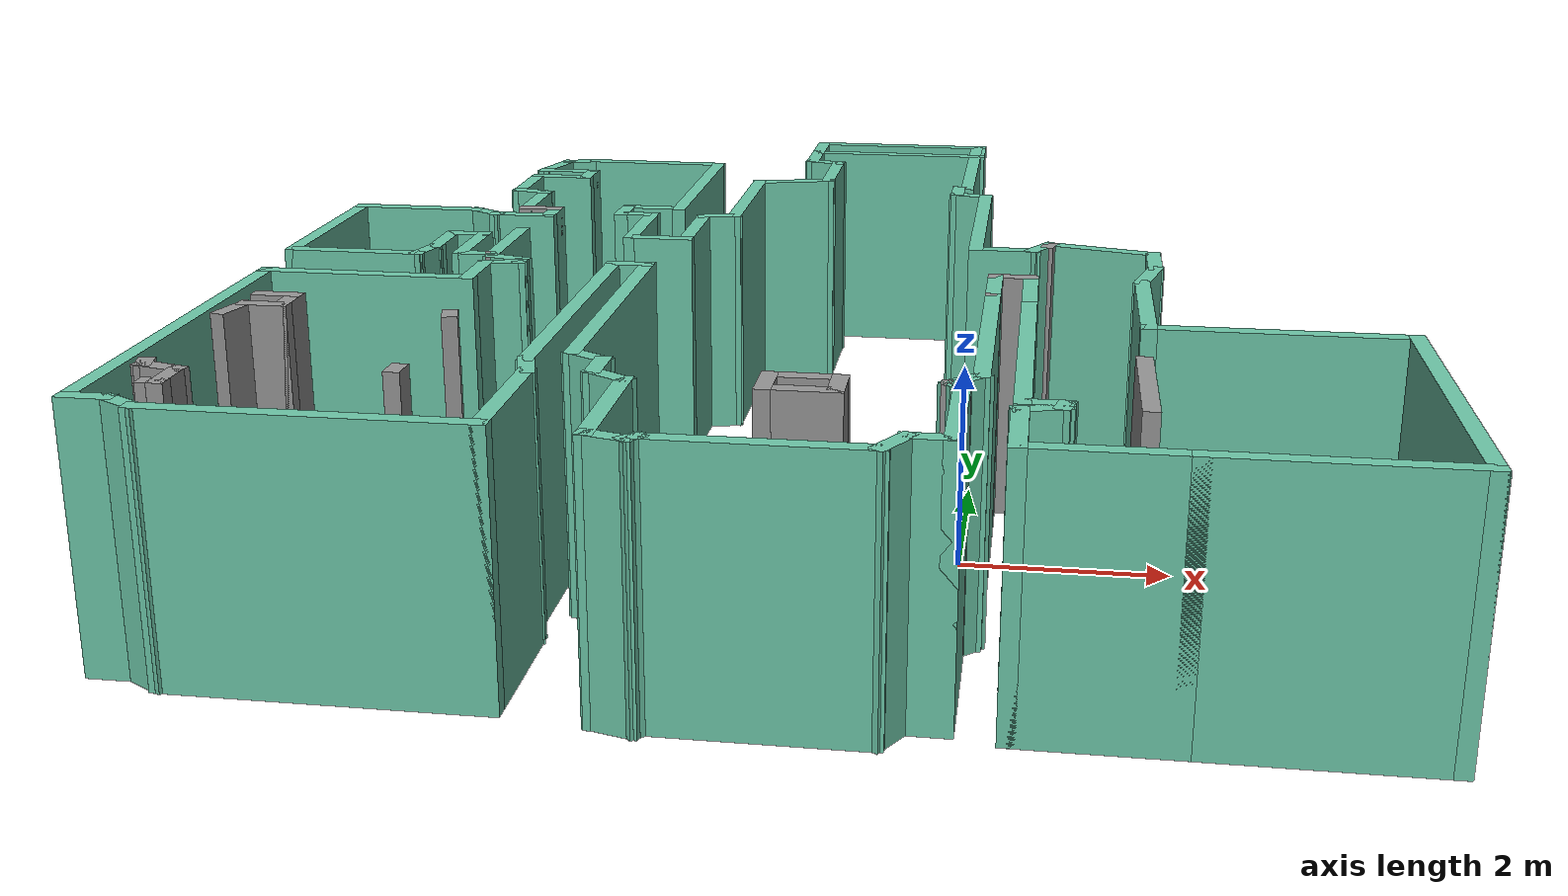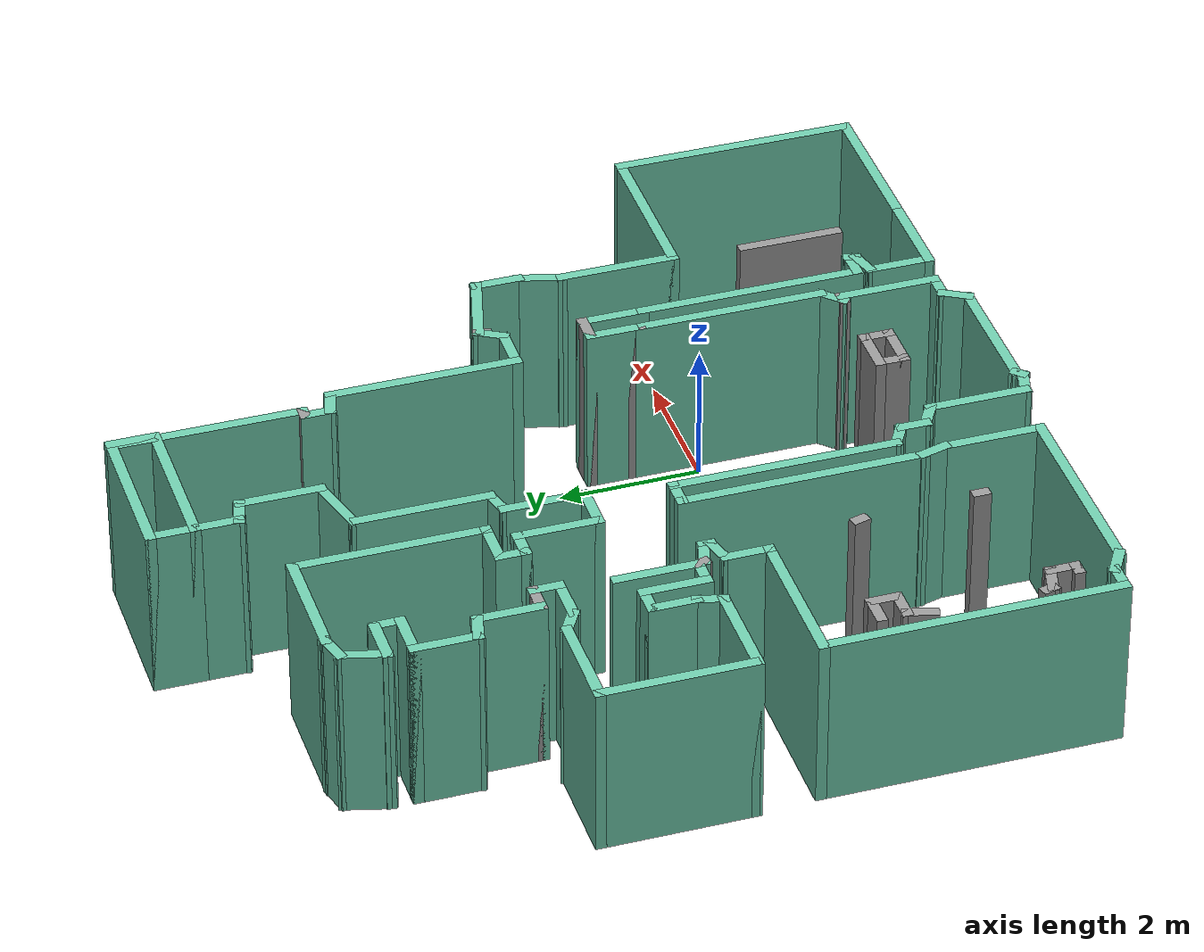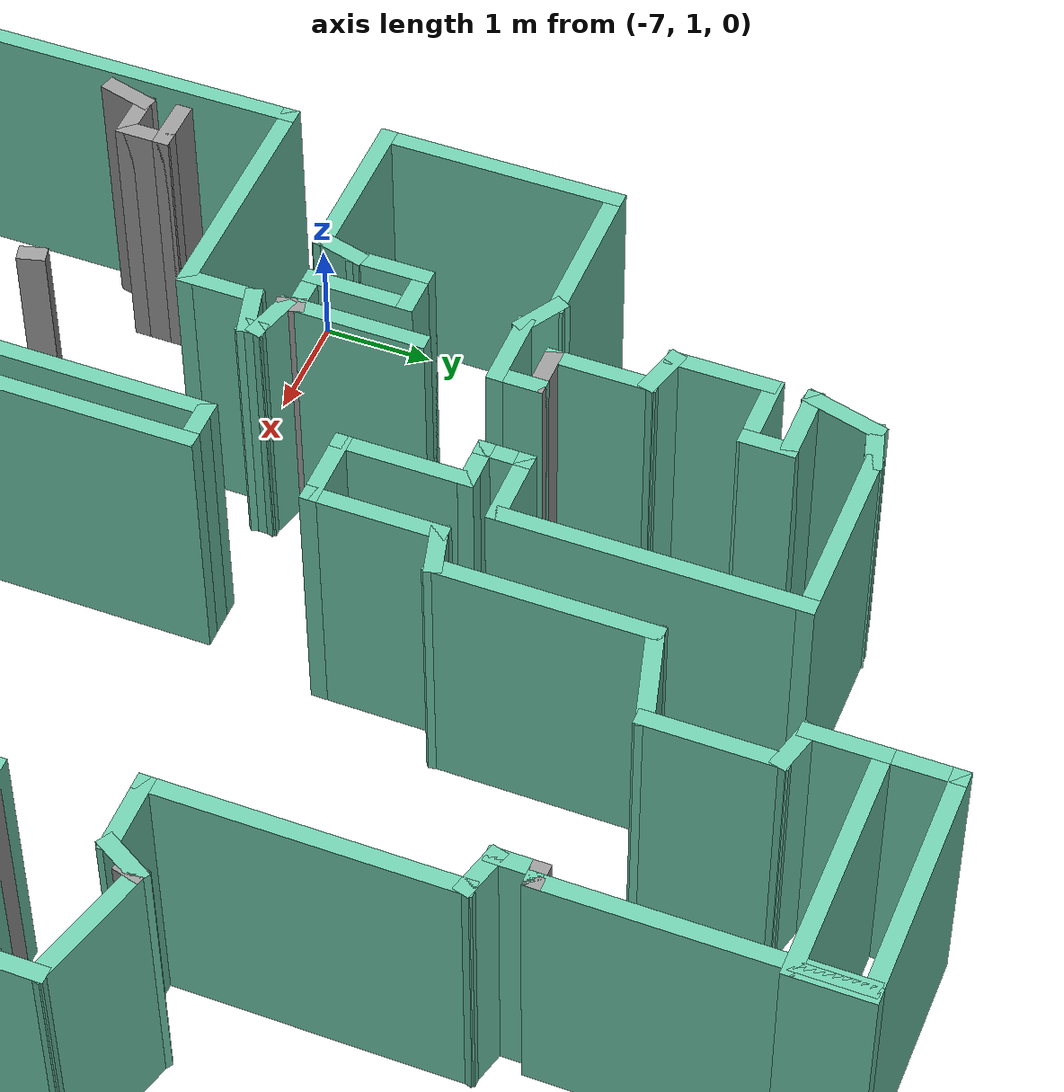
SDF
<?xml version='1.0'?>
<sdf version='1.6'>
  <model name='map_3'>
    <pose frame=''>-1.57368 2.22942 0 0 -0 0</pose>
    <link name='Wall_0'>
      <collision name='Wall_0_Collision'>
        <geometry>
          <box>
            <size>2.25 0.15 2.5</size>
          </box>
        </geometry>
        <pose frame=''>0 0 1.25 0 -0 0</pose>
      </collision>
      <visual name='Wall_0_Visual'>
        <pose frame=''>0 0 1.25 0 -0 0</pose>
        <geometry>
          <box>
            <size>2.25 0.15 2.5</size>
          </box>
        </geometry>
        <material>
          <script>
            <uri>file://media/materials/scripts/gazebo.material</uri>
            <name>Gazebo/Grey</name>
          </script>
          <ambient>0.435294 0.796078 0.67451 1</ambient>
        </material>
        <meta>
          <layer>0</layer>
        </meta>
      </visual>
      <pose frame=''>0.303175 6.04258 0 0 -0 3.14159</pose>
    </link>
    <link name='Wall_1'>
      <collision name='Wall_1_Collision'>
        <geometry>
          <box>
            <size>0.75 0.15 2.5</size>
          </box>
        </geometry>
        <pose frame=''>0 0 1.25 0 -0 0</pose>
      </collision>
      <visual name='Wall_1_Visual'>
        <pose frame=''>0 0 1.25 0 -0 0</pose>
        <geometry>
          <box>
            <size>0.75 0.15 2.5</size>
          </box>
        </geometry>
        <material>
          <script>
            <uri>file://media/materials/scripts/gazebo.material</uri>
            <name>Gazebo/Grey</name>
          </script>
          <ambient>0.435294 0.796078 0.67451 1</ambient>
        </material>
        <meta>
          <layer>0</layer>
        </meta>
      </visual>
      <pose frame=''>-0.746825 5.74258 0 0 -0 -1.5708</pose>
    </link>
    <link name='Wall_10'>
      <collision name='Wall_10_Collision'>
        <geometry>
          <box>
            <size>0.5 0.15 2.5</size>
          </box>
        </geometry>
        <pose frame=''>0 0 1.25 0 -0 0</pose>
      </collision>
      <visual name='Wall_10_Visual'>
        <pose frame=''>0 0 1.25 0 -0 0</pose>
        <geometry>
          <box>
            <size>0.5 0.15 2.5</size>
          </box>
        </geometry>
        <material>
          <script>
            <uri>file://media/materials/scripts/gazebo.material</uri>
            <name>Gazebo/Grey</name>
          </script>
          <ambient>0.435294 0.796078 0.67451 1</ambient>
        </material>
        <meta>
          <layer>0</layer>
        </meta>
      </visual>
      <pose frame=''>-1.39882 1.53671 0 0 -0 -2.87979</pose>
    </link>
    <link name='Wall_100'>
      <collision name='Wall_100_Collision'>
        <geometry>
          <box>
            <size>1.75 0.15 2.5</size>
          </box>
        </geometry>
        <pose frame=''>0 0 1.25 0 -0 0</pose>
      </collision>
      <visual name='Wall_100_Visual'>
        <pose frame=''>0 0 1.25 0 -0 0</pose>
        <geometry>
          <box>
            <size>1.75 0.15 2.5</size>
          </box>
        </geometry>
        <material>
          <script>
            <uri>file://media/materials/scripts/gazebo.material</uri>
            <name>Gazebo/Grey</name>
          </script>
          <ambient>0.435294 0.796078 0.67451 1</ambient>
        </material>
        <meta>
          <layer>0</layer>
        </meta>
      </visual>
      <pose frame=''>3.22626 -1.57739 0 0 -0 1.5708</pose>
    </link>
    <link name='Wall_101'>
      <collision name='Wall_101_Collision'>
        <geometry>
          <box>
            <size>0.75 0.15 2.5</size>
          </box>
        </geometry>
        <pose frame=''>0 0 1.25 0 -0 0</pose>
      </collision>
      <visual name='Wall_101_Visual'>
        <pose frame=''>0 0 1.25 0 -0 0</pose>
        <geometry>
          <box>
            <size>0.75 0.15 2.5</size>
          </box>
        </geometry>
        <material>
          <script>
            <uri>file://media/materials/scripts/gazebo.material</uri>
            <name>Gazebo/Grey</name>
          </script>
          <ambient>0.435294 0.796078 0.67451 1</ambient>
        </material>
        <meta>
          <layer>0</layer>
        </meta>
      </visual>
      <pose frame=''>3.30391 -0.487613 0 0 -0 1.309</pose>
    </link>
    <link name='Wall_102'>
      <collision name='Wall_102_Collision'>
        <geometry>
          <box>
            <size>0.75 0.15 2.5</size>
          </box>
        </geometry>
        <pose frame=''>0 0 1.25 0 -0 0</pose>
      </collision>
      <visual name='Wall_102_Visual'>
        <pose frame=''>0 0 1.25 0 -0 0</pose>
        <geometry>
          <box>
            <size>0.75 0.15 2.5</size>
          </box>
        </geometry>
        <material>
          <script>
            <uri>file://media/materials/scripts/gazebo.material</uri>
            <name>Gazebo/Grey</name>
          </script>
          <ambient>0.435294 0.796078 0.67451 1</ambient>
        </material>
        <meta>
          <layer>0</layer>
        </meta>
      </visual>
      <pose frame=''>3.38155 0.102165 0 0 -0 1.5708</pose>
    </link>
    <link name='Wall_103'>
      <collision name='Wall_103_Collision'>
        <geometry>
          <box>
            <size>1.25 0.15 2.5</size>
          </box>
        </geometry>
        <pose frame=''>0 0 1.25 0 -0 0</pose>
      </collision>
      <visual name='Wall_103_Visual'>
        <pose frame=''>0 0 1.25 0 -0 0</pose>
        <geometry>
          <box>
            <size>1.25 0.15 2.5</size>
          </box>
        </geometry>
        <material>
          <script>
            <uri>file://media/materials/scripts/gazebo.material</uri>
            <name>Gazebo/Grey</name>
          </script>
          <ambient>0.435294 0.796078 0.67451 1</ambient>
        </material>
        <meta>
          <layer>0</layer>
        </meta>
      </visual>
      <pose frame=''>2.85029 0.544515 0 0 -0 2.87979</pose>
    </link>
    <link name='Wall_104'>
      <collision name='Wall_104_Collision'>
        <geometry>
          <box>
            <size>0.25 0.15 2.5</size>
          </box>
        </geometry>
        <pose frame=''>0 0 1.25 0 -0 0</pose>
      </collision>
      <visual name='Wall_104_Visual'>
        <pose frame=''>0 0 1.25 0 -0 0</pose>
        <geometry>
          <box>
            <size>0.25 0.15 2.5</size>
          </box>
        </geometry>
        <material>
          <script>
            <uri>file://media/materials/scripts/gazebo.material</uri>
            <name>Gazebo/Grey</name>
          </script>
          <ambient>1 1 1 1</ambient>
        </material>
        <meta>
          <layer>0</layer>
        </meta>
      </visual>
      <pose frame=''>2.30609 0.638569 0 0 -0 -1.8326</pose>
    </link>
    <link name='Wall_108'>
      <collision name='Wall_108_Collision'>
        <geometry>
          <box>
            <size>0.5 0.15 2.5</size>
          </box>
        </geometry>
        <pose frame=''>0 0 1.25 0 -0 0</pose>
      </collision>
      <visual name='Wall_108_Visual'>
        <pose frame=''>0 0 1.25 0 -0 0</pose>
        <geometry>
          <box>
            <size>0.5 0.15 2.5</size>
          </box>
        </geometry>
        <material>
          <script>
            <uri>file://media/materials/scripts/gazebo.material</uri>
            <name>Gazebo/Grey</name>
          </script>
          <ambient>0.435294 0.796078 0.67451 1</ambient>
        </material>
        <meta>
          <layer>0</layer>
        </meta>
      </visual>
      <pose frame=''>2.23154 0.535311 0 0 -0 -2.0944</pose>
    </link>
    <link name='Wall_109'>
      <collision name='Wall_109_Collision'>
        <geometry>
          <box>
            <size>0.75 0.15 2.5</size>
          </box>
        </geometry>
        <pose frame=''>0 0 1.25 0 -0 0</pose>
      </collision>
      <visual name='Wall_109_Visual'>
        <pose frame=''>0 0 1.25 0 -0 0</pose>
        <geometry>
          <box>
            <size>0.75 0.15 2.5</size>
          </box>
        </geometry>
        <material>
          <script>
            <uri>file://media/materials/scripts/gazebo.material</uri>
            <name>Gazebo/Grey</name>
          </script>
          <ambient>0.435294 0.796078 0.67451 1</ambient>
        </material>
        <meta>
          <layer>0</layer>
        </meta>
      </visual>
      <pose frame=''>1.84404 0.383757 0 0 -0 3.14159</pose>
    </link>
    <link name='Wall_11'>
      <collision name='Wall_11_Collision'>
        <geometry>
          <box>
            <size>1.25 0.15 2.5</size>
          </box>
        </geometry>
        <pose frame=''>0 0 1.25 0 -0 0</pose>
      </collision>
      <visual name='Wall_11_Visual'>
        <pose frame=''>0 0 1.25 0 -0 0</pose>
        <geometry>
          <box>
            <size>1.25 0.15 2.5</size>
          </box>
        </geometry>
        <material>
          <script>
            <uri>file://media/materials/scripts/gazebo.material</uri>
            <name>Gazebo/Grey</name>
          </script>
          <ambient>0.435294 0.796078 0.67451 1</ambient>
        </material>
        <meta>
          <layer>0</layer>
        </meta>
      </visual>
      <pose frame=''>-1.56786 0.941415 0 0 -0 -1.5708</pose>
    </link>
    <link name='Wall_110'>
      <collision name='Wall_110_Collision'>
        <geometry>
          <box>
            <size>2.75 0.15 2.5</size>
          </box>
        </geometry>
        <pose frame=''>0 0 1.25 0 -0 0</pose>
      </collision>
      <visual name='Wall_110_Visual'>
        <pose frame=''>0 0 1.25 0 -0 0</pose>
        <geometry>
          <box>
            <size>2.75 0.15 2.5</size>
          </box>
        </geometry>
        <material>
          <script>
            <uri>file://media/materials/scripts/gazebo.material</uri>
            <name>Gazebo/Grey</name>
          </script>
          <ambient>0.435294 0.796078 0.67451 1</ambient>
        </material>
        <meta>
          <layer>0</layer>
        </meta>
      </visual>
      <pose frame=''>1.54404 1.68376 0 0 -0 1.5708</pose>
    </link>
    <link name='Wall_111'>
      <collision name='Wall_111_Collision'>
        <geometry>
          <box>
            <size>0.5 0.15 2.5</size>
          </box>
        </geometry>
        <pose frame=''>0 0 1.25 0 -0 0</pose>
      </collision>
      <visual name='Wall_111_Visual'>
        <pose frame=''>0 0 1.25 0 -0 0</pose>
        <geometry>
          <box>
            <size>0.5 0.15 2.5</size>
          </box>
        </geometry>
        <material>
          <script>
            <uri>file://media/materials/scripts/gazebo.material</uri>
            <name>Gazebo/Grey</name>
          </script>
          <ambient>0.435294 0.796078 0.67451 1</ambient>
        </material>
        <meta>
          <layer>0</layer>
        </meta>
      </visual>
      <pose frame=''>1.375 3.02905 0 0 -0 2.87979</pose>
    </link>
    <link name='Wall_112'>
      <collision name='Wall_112_Collision'>
        <geometry>
          <box>
            <size>0.5 0.15 2.5</size>
          </box>
        </geometry>
        <pose frame=''>0 0 1.25 0 -0 0</pose>
      </collision>
      <visual name='Wall_112_Visual'>
        <pose frame=''>0 0 1.25 0 -0 0</pose>
        <geometry>
          <box>
            <size>0.5 0.15 2.5</size>
          </box>
        </geometry>
        <material>
          <script>
            <uri>file://media/materials/scripts/gazebo.material</uri>
            <name>Gazebo/Grey</name>
          </script>
          <ambient>0.435294 0.796078 0.67451 1</ambient>
        </material>
        <meta>
          <layer>0</layer>
        </meta>
      </visual>
      <pose frame=''>1.20596 3.24934 0 0 -0 1.5708</pose>
    </link>
    <link name='Wall_113'>
      <collision name='Wall_113_Collision'>
        <geometry>
          <box>
            <size>0.25 0.15 2.5</size>
          </box>
        </geometry>
        <pose frame=''>0 0 1.25 0 -0 0</pose>
      </collision>
      <visual name='Wall_113_Visual'>
        <pose frame=''>0 0 1.25 0 -0 0</pose>
        <geometry>
          <box>
            <size>0.25 0.15 2.5</size>
          </box>
        </geometry>
        <material>
          <script>
            <uri>file://media/materials/scripts/gazebo.material</uri>
            <name>Gazebo/Grey</name>
          </script>
          <ambient>1 1 1 1</ambient>
        </material>
        <meta>
          <layer>0</layer>
        </meta>
      </visual>
      <pose frame=''>1.25596 3.42434 0 0 -0 0</pose>
    </link>
    <link name='Wall_114'>
      <collision name='Wall_114_Collision'>
        <geometry>
          <box>
            <size>2.75 0.15 2.5</size>
          </box>
        </geometry>
        <pose frame=''>0 0 1.25 0 -0 0</pose>
      </collision>
      <visual name='Wall_114_Visual'>
        <pose frame=''>0 0 1.25 0 -0 0</pose>
        <geometry>
          <box>
            <size>2.75 0.15 2.5</size>
          </box>
        </geometry>
        <material>
          <script>
            <uri>file://media/materials/scripts/gazebo.material</uri>
            <name>Gazebo/Grey</name>
          </script>
          <ambient>0.435294 0.796078 0.67451 1</ambient>
        </material>
        <meta>
          <layer>0</layer>
        </meta>
      </visual>
      <pose frame=''>1.30596 4.72434 0 0 -0 1.5708</pose>
    </link>
    <link name='Wall_12'>
      <collision name='Wall_12_Collision'>
        <geometry>
          <box>
            <size>0.75 0.15 2.5</size>
          </box>
        </geometry>
        <pose frame=''>0 0 1.25 0 -0 0</pose>
      </collision>
      <visual name='Wall_12_Visual'>
        <pose frame=''>0 0 1.25 0 -0 0</pose>
        <geometry>
          <box>
            <size>0.75 0.15 2.5</size>
          </box>
        </geometry>
        <material>
          <script>
            <uri>file://media/materials/scripts/gazebo.material</uri>
            <name>Gazebo/Grey</name>
          </script>
          <ambient>0.435294 0.796078 0.67451 1</ambient>
        </material>
        <meta>
          <layer>0</layer>
        </meta>
      </visual>
      <pose frame=''>-1.86786 0.391415 0 0 -0 3.14159</pose>
    </link>
    <link name='Wall_125'>
      <collision name='Wall_125_Collision'>
        <geometry>
          <box>
            <size>0.5 0.15 2.5</size>
          </box>
        </geometry>
        <pose frame=''>0 0 1.25 0 -0 0</pose>
      </collision>
      <visual name='Wall_125_Visual'>
        <pose frame=''>0 0 1.25 0 -0 0</pose>
        <geometry>
          <box>
            <size>0.5 0.15 2.5</size>
          </box>
        </geometry>
        <material>
          <script>
            <uri>file://media/materials/scripts/gazebo.material</uri>
            <name>Gazebo/Grey</name>
          </script>
          <ambient>1 1 1 1</ambient>
        </material>
        <meta>
          <layer>0</layer>
        </meta>
      </visual>
      <pose frame=''>0.031075 -4.44181 0 0 -0 -1.5708</pose>
    </link>
    <link name='Wall_126'>
      <collision name='Wall_126_Collision'>
        <geometry>
          <box>
            <size>0.75 0.15 2.5</size>
          </box>
        </geometry>
        <pose frame=''>0 0 1.25 0 -0 0</pose>
      </collision>
      <visual name='Wall_126_Visual'>
        <pose frame=''>0 0 1.25 0 -0 0</pose>
        <geometry>
          <box>
            <size>0.75 0.15 2.5</size>
          </box>
        </geometry>
        <material>
          <script>
            <uri>file://media/materials/scripts/gazebo.material</uri>
            <name>Gazebo/Grey</name>
          </script>
          <ambient>1 1 1 1</ambient>
        </material>
        <meta>
          <layer>0</layer>
        </meta>
      </visual>
      <pose frame=''>0.331075 -4.61681 0 0 -0 0</pose>
    </link>
    <link name='Wall_127'>
      <collision name='Wall_127_Collision'>
        <geometry>
          <box>
            <size>0.5 0.15 2.5</size>
          </box>
        </geometry>
        <pose frame=''>0 0 1.25 0 -0 0</pose>
      </collision>
      <visual name='Wall_127_Visual'>
        <pose frame=''>0 0 1.25 0 -0 0</pose>
        <geometry>
          <box>
            <size>0.5 0.15 2.5</size>
          </box>
        </geometry>
        <material>
          <script>
            <uri>file://media/materials/scripts/gazebo.material</uri>
            <name>Gazebo/Grey</name>
          </script>
          <ambient>1 1 1 1</ambient>
        </material>
        <meta>
          <layer>0</layer>
        </meta>
      </visual>
      <pose frame=''>0.631075 -4.44181 0 0 -0 1.5708</pose>
    </link>
    <link name='Wall_128'>
      <collision name='Wall_128_Collision'>
        <geometry>
          <box>
            <size>0.75 0.15 2.5</size>
          </box>
        </geometry>
        <pose frame=''>0 0 1.25 0 -0 0</pose>
      </collision>
      <visual name='Wall_128_Visual'>
        <pose frame=''>0 0 1.25 0 -0 0</pose>
        <geometry>
          <box>
            <size>0.75 0.15 2.5</size>
          </box>
        </geometry>
        <material>
          <script>
            <uri>file://media/materials/scripts/gazebo.material</uri>
            <name>Gazebo/Grey</name>
          </script>
          <ambient>1 1 1 1</ambient>
        </material>
        <meta>
          <layer>0</layer>
        </meta>
      </visual>
      <pose frame=''>0.331075 -4.26681 0 0 -0 3.14159</pose>
    </link>
    <link name='Wall_130'>
      <collision name='Wall_130_Collision'>
        <geometry>
          <box>
            <size>1.5 0.15 2.5</size>
          </box>
        </geometry>
        <pose frame=''>0 0 1.25 0 -0 0</pose>
      </collision>
      <visual name='Wall_130_Visual'>
        <pose frame=''>0 0 1.25 0 -0 0</pose>
        <geometry>
          <box>
            <size>1.5 0.15 2.5</size>
          </box>
        </geometry>
        <material>
          <script>
            <uri>file://media/materials/scripts/gazebo.material</uri>
            <name>Gazebo/Grey</name>
          </script>
          <ambient>1 1 1 1</ambient>
        </material>
        <meta>
          <layer>0</layer>
        </meta>
      </visual>
      <pose frame=''>3.15108 -4.06181 0 0 -0 -1.5708</pose>
    </link>
    <link name='Wall_132'>
      <collision name='Wall_132_Collision'>
        <geometry>
          <box>
            <size>0.25 0.15 2.5</size>
          </box>
        </geometry>
        <pose frame=''>0 0 1.25 0 -0 0</pose>
      </collision>
      <visual name='Wall_132_Visual'>
        <pose frame=''>0 0 1.25 0 -0 0</pose>
        <geometry>
          <box>
            <size>0.25 0.15 2.5</size>
          </box>
        </geometry>
        <material>
          <script>
            <uri>file://media/materials/scripts/gazebo.material</uri>
            <name>Gazebo/Grey</name>
          </script>
          <ambient>1 1 1 1</ambient>
        </material>
        <meta>
          <layer>0</layer>
        </meta>
      </visual>
      <pose frame=''>-3.17598 -2.85511 0 0 -0 -1.309</pose>
    </link>
    <link name='Wall_134'>
      <collision name='Wall_134_Collision'>
        <geometry>
          <box>
            <size>0.25 0.15 2.5</size>
          </box>
        </geometry>
        <pose frame=''>0 0 1.25 0 -0 0</pose>
      </collision>
      <visual name='Wall_134_Visual'>
        <pose frame=''>0 0 1.25 0 -0 0</pose>
        <geometry>
          <box>
            <size>0.25 0.15 2.5</size>
          </box>
        </geometry>
        <material>
          <script>
            <uri>file://media/materials/scripts/gazebo.material</uri>
            <name>Gazebo/Grey</name>
          </script>
          <ambient>1 1 1 1</ambient>
        </material>
        <meta>
          <layer>0</layer>
        </meta>
      </visual>
      <pose frame=''>-3.10893 -4.55681 0 0 -0 -1.5708</pose>
    </link>
    <link name='Wall_138'>
      <collision name='Wall_138_Collision'>
        <geometry>
          <box>
            <size>0.5 0.15 2.5</size>
          </box>
        </geometry>
        <pose frame=''>0 0 1.25 0 -0 0</pose>
      </collision>
      <visual name='Wall_138_Visual'>
        <pose frame=''>0 0 1.25 0 -0 0</pose>
        <geometry>
          <box>
            <size>0.5 0.15 2.5</size>
          </box>
        </geometry>
        <material>
          <script>
            <uri>file://media/materials/scripts/gazebo.material</uri>
            <name>Gazebo/Grey</name>
          </script>
          <ambient>1 1 1 1</ambient>
        </material>
        <meta>
          <layer>0</layer>
        </meta>
      </visual>
      <pose frame=''>-5.02718 -2.4211 0 0 -0 0</pose>
    </link>
    <link name='Wall_139'>
      <collision name='Wall_139_Collision'>
        <geometry>
          <box>
            <size>0.5 0.15 2.5</size>
          </box>
        </geometry>
        <pose frame=''>0 0 1.25 0 -0 0</pose>
      </collision>
      <visual name='Wall_139_Visual'>
        <pose frame=''>0 0 1.25 0 -0 0</pose>
        <geometry>
          <box>
            <size>0.5 0.15 2.5</size>
          </box>
        </geometry>
        <material>
          <script>
            <uri>file://media/materials/scripts/gazebo.material</uri>
            <name>Gazebo/Grey</name>
          </script>
          <ambient>1 1 1 1</ambient>
        </material>
        <meta>
          <layer>0</layer>
        </meta>
      </visual>
      <pose frame=''>-4.85218 -2.5961 0 0 -0 -1.5708</pose>
    </link>
    <link name='Wall_140'>
      <collision name='Wall_140_Collision'>
        <geometry>
          <box>
            <size>0.5 0.15 2.5</size>
          </box>
        </geometry>
        <pose frame=''>0 0 1.25 0 -0 0</pose>
      </collision>
      <visual name='Wall_140_Visual'>
        <pose frame=''>0 0 1.25 0 -0 0</pose>
        <geometry>
          <box>
            <size>0.5 0.15 2.5</size>
          </box>
        </geometry>
        <material>
          <script>
            <uri>file://media/materials/scripts/gazebo.material</uri>
            <name>Gazebo/Grey</name>
          </script>
          <ambient>1 1 1 1</ambient>
        </material>
        <meta>
          <layer>0</layer>
        </meta>
      </visual>
      <pose frame=''>-5.02718 -2.7711 0 0 -0 3.14159</pose>
    </link>
    <link name='Wall_141'>
      <collision name='Wall_141_Collision'>
        <geometry>
          <box>
            <size>0.5 0.15 2.5</size>
          </box>
        </geometry>
        <pose frame=''>0 0 1.25 0 -0 0</pose>
      </collision>
      <visual name='Wall_141_Visual'>
        <pose frame=''>0 0 1.25 0 -0 0</pose>
        <geometry>
          <box>
            <size>0.5 0.15 2.5</size>
          </box>
        </geometry>
        <material>
          <script>
            <uri>file://media/materials/scripts/gazebo.material</uri>
            <name>Gazebo/Grey</name>
          </script>
          <ambient>1 1 1 1</ambient>
        </material>
        <meta>
          <layer>0</layer>
        </meta>
      </visual>
      <pose frame=''>-5.24747 -2.94014 0 0 -0 -1.8326</pose>
    </link>
    <link name='Wall_144'>
      <collision name='Wall_144_Collision'>
        <geometry>
          <box>
            <size>0.25 0.15 2.5</size>
          </box>
        </geometry>
        <pose frame=''>0 0 1.25 0 -0 0</pose>
      </collision>
      <visual name='Wall_144_Visual'>
        <pose frame=''>0 0 1.25 0 -0 0</pose>
        <geometry>
          <box>
            <size>0.25 0.15 2.5</size>
          </box>
        </geometry>
        <material>
          <script>
            <uri>file://media/materials/scripts/gazebo.material</uri>
            <name>Gazebo/Grey</name>
          </script>
          <ambient>1 1 1 1</ambient>
        </material>
        <meta>
          <layer>0</layer>
        </meta>
      </visual>
      <pose frame=''>-5.28923 -4.6894 0 0 -0 -1.309</pose>
    </link>
    <link name='Wall_145'>
      <collision name='Wall_145_Collision'>
        <geometry>
          <box>
            <size>0.5 0.15 2.5</size>
          </box>
        </geometry>
        <pose frame=''>0 0 1.25 0 -0 0</pose>
      </collision>
      <visual name='Wall_145_Visual'>
        <pose frame=''>0 0 1.25 0 -0 0</pose>
        <geometry>
          <box>
            <size>0.5 0.15 2.5</size>
          </box>
        </geometry>
        <material>
          <script>
            <uri>file://media/materials/scripts/gazebo.material</uri>
            <name>Gazebo/Grey</name>
          </script>
          <ambient>1 1 1 1</ambient>
        </material>
        <meta>
          <layer>0</layer>
        </meta>
      </visual>
      <pose frame=''>-5.10726 -4.78299 0 0 -0 -0.261799</pose>
    </link>
    <link name='Wall_146'>
      <collision name='Wall_146_Collision'>
        <geometry>
          <box>
            <size>0.5 0.15 2.5</size>
          </box>
        </geometry>
        <pose frame=''>0 0 1.25 0 -0 0</pose>
      </collision>
      <visual name='Wall_146_Visual'>
        <pose frame=''>0 0 1.25 0 -0 0</pose>
        <geometry>
          <box>
            <size>0.5 0.15 2.5</size>
          </box>
        </geometry>
        <material>
          <script>
            <uri>file://media/materials/scripts/gazebo.material</uri>
            <name>Gazebo/Grey</name>
          </script>
          <ambient>1 1 1 1</ambient>
        </material>
        <meta>
          <layer>0</layer>
        </meta>
      </visual>
      <pose frame=''>-4.93822 -5.00328 0 0 -0 -1.5708</pose>
    </link>
    <link name='Wall_147'>
      <collision name='Wall_147_Collision'>
        <geometry>
          <box>
            <size>0.25 0.15 2.5</size>
          </box>
        </geometry>
        <pose frame=''>0 0 1.25 0 -0 0</pose>
      </collision>
      <visual name='Wall_147_Visual'>
        <pose frame=''>0 0 1.25 0 -0 0</pose>
        <geometry>
          <box>
            <size>0.25 0.15 2.5</size>
          </box>
        </geometry>
        <material>
          <script>
            <uri>file://media/materials/scripts/gazebo.material</uri>
            <name>Gazebo/Grey</name>
          </script>
          <ambient>1 1 1 1</ambient>
        </material>
        <meta>
          <layer>0</layer>
        </meta>
      </visual>
      <pose frame=''>-4.98822 -5.17828 0 0 -0 3.14159</pose>
    </link>
    <link name='Wall_18'>
      <collision name='Wall_18_Collision'>
        <geometry>
          <box>
            <size>1.25 0.15 2.5</size>
          </box>
        </geometry>
        <pose frame=''>0 0 1.25 0 -0 0</pose>
      </collision>
      <visual name='Wall_18_Visual'>
        <pose frame=''>0 0 1.25 0 -0 0</pose>
        <geometry>
          <box>
            <size>1.25 0.15 2.5</size>
          </box>
        </geometry>
        <material>
          <script>
            <uri>file://media/materials/scripts/gazebo.material</uri>
            <name>Gazebo/Grey</name>
          </script>
          <ambient>0.435294 0.796078 0.67451 1</ambient>
        </material>
        <meta>
          <layer>0</layer>
        </meta>
      </visual>
      <pose frame=''>-2.16786 0.941415 0 0 -0 1.5708</pose>
    </link>
    <link name='Wall_19'>
      <collision name='Wall_19_Collision'>
        <geometry>
          <box>
            <size>0.5 0.15 2.5</size>
          </box>
        </geometry>
        <pose frame=''>0 0 1.25 0 -0 0</pose>
      </collision>
      <visual name='Wall_19_Visual'>
        <pose frame=''>0 0 1.25 0 -0 0</pose>
        <geometry>
          <box>
            <size>0.5 0.15 2.5</size>
          </box>
        </geometry>
        <material>
          <script>
            <uri>file://media/materials/scripts/gazebo.material</uri>
            <name>Gazebo/Grey</name>
          </script>
          <ambient>0.435294 0.796078 0.67451 1</ambient>
        </material>
        <meta>
          <layer>0</layer>
        </meta>
      </visual>
      <pose frame=''>-2.34286 1.49141 0 0 -0 3.14159</pose>
    </link>
    <link name='Wall_2'>
      <collision name='Wall_2_Collision'>
        <geometry>
          <box>
            <size>2.25 0.15 2.5</size>
          </box>
        </geometry>
        <pose frame=''>0 0 1.25 0 -0 0</pose>
      </collision>
      <visual name='Wall_2_Visual'>
        <pose frame=''>0 0 1.25 0 -0 0</pose>
        <geometry>
          <box>
            <size>2.25 0.15 2.5</size>
          </box>
        </geometry>
        <material>
          <script>
            <uri>file://media/materials/scripts/gazebo.material</uri>
            <name>Gazebo/Grey</name>
          </script>
          <ambient>0.435294 0.796078 0.67451 1</ambient>
        </material>
        <meta>
          <layer>0</layer>
        </meta>
      </visual>
      <pose frame=''>0.303175 5.44259 0 0 -0 0</pose>
    </link>
    <link name='Wall_22'>
      <collision name='Wall_22_Collision'>
        <geometry>
          <box>
            <size>0.5 0.15 2.5</size>
          </box>
        </geometry>
        <pose frame=''>0 0 1.25 0 -0 0</pose>
      </collision>
      <visual name='Wall_22_Visual'>
        <pose frame=''>0 0 1.25 0 -0 0</pose>
        <geometry>
          <box>
            <size>0.5 0.15 2.5</size>
          </box>
        </geometry>
        <material>
          <script>
            <uri>file://media/materials/scripts/gazebo.material</uri>
            <name>Gazebo/Grey</name>
          </script>
          <ambient>0.435294 0.796078 0.67451 1</ambient>
        </material>
        <meta>
          <layer>0</layer>
        </meta>
      </visual>
      <pose frame=''>-2.51786 1.66641 0 0 -0 1.5708</pose>
    </link>
    <link name='Wall_23'>
      <collision name='Wall_23_Collision'>
        <geometry>
          <box>
            <size>0.75 0.15 2.5</size>
          </box>
        </geometry>
        <pose frame=''>0 0 1.25 0 -0 0</pose>
      </collision>
      <visual name='Wall_23_Visual'>
        <pose frame=''>0 0 1.25 0 -0 0</pose>
        <geometry>
          <box>
            <size>0.75 0.15 2.5</size>
          </box>
        </geometry>
        <material>
          <script>
            <uri>file://media/materials/scripts/gazebo.material</uri>
            <name>Gazebo/Grey</name>
          </script>
          <ambient>0.435294 0.796078 0.67451 1</ambient>
        </material>
        <meta>
          <layer>0</layer>
        </meta>
      </visual>
      <pose frame=''>-2.21786 1.84142 0 0 -0 0</pose>
    </link>
    <link name='Wall_24'>
      <collision name='Wall_24_Collision'>
        <geometry>
          <box>
            <size>2.75 0.15 2.5</size>
          </box>
        </geometry>
        <pose frame=''>0 0 1.25 0 -0 0</pose>
      </collision>
      <visual name='Wall_24_Visual'>
        <pose frame=''>0 0 1.25 0 -0 0</pose>
        <geometry>
          <box>
            <size>2.75 0.15 2.5</size>
          </box>
        </geometry>
        <material>
          <script>
            <uri>file://media/materials/scripts/gazebo.material</uri>
            <name>Gazebo/Grey</name>
          </script>
          <ambient>0.435294 0.796078 0.67451 1</ambient>
        </material>
        <meta>
          <layer>0</layer>
        </meta>
      </visual>
      <pose frame=''>-1.91786 3.14141 0 0 -0 1.5708</pose>
    </link>
    <link name='Wall_25'>
      <collision name='Wall_25_Collision'>
        <geometry>
          <box>
            <size>1.75 0.15 2.5</size>
          </box>
        </geometry>
        <pose frame=''>0 0 1.25 0 -0 0</pose>
      </collision>
      <visual name='Wall_25_Visual'>
        <pose frame=''>0 0 1.25 0 -0 0</pose>
        <geometry>
          <box>
            <size>1.75 0.15 2.5</size>
          </box>
        </geometry>
        <material>
          <script>
            <uri>file://media/materials/scripts/gazebo.material</uri>
            <name>Gazebo/Grey</name>
          </script>
          <ambient>0.435294 0.796078 0.67451 1</ambient>
        </material>
        <meta>
          <layer>0</layer>
        </meta>
      </visual>
      <pose frame=''>-2.71786 4.44142 0 0 -0 3.14159</pose>
    </link>
    <link name='Wall_26'>
      <collision name='Wall_26_Collision'>
        <geometry>
          <box>
            <size>0.5 0.15 2.5</size>
          </box>
        </geometry>
        <pose frame=''>0 0 1.25 0 -0 0</pose>
      </collision>
      <visual name='Wall_26_Visual'>
        <pose frame=''>0 0 1.25 0 -0 0</pose>
        <geometry>
          <box>
            <size>0.5 0.15 2.5</size>
          </box>
        </geometry>
        <material>
          <script>
            <uri>file://media/materials/scripts/gazebo.material</uri>
            <name>Gazebo/Grey</name>
          </script>
          <ambient>0.435294 0.796078 0.67451 1</ambient>
        </material>
        <meta>
          <layer>0</layer>
        </meta>
      </visual>
      <pose frame=''>-3.6869 4.39612 0 0 -0 -2.87979</pose>
    </link>
    <link name='Wall_27'>
      <collision name='Wall_27_Collision'>
        <geometry>
          <box>
            <size>0.75 0.15 2.5</size>
          </box>
        </geometry>
        <pose frame=''>0 0 1.25 0 -0 0</pose>
      </collision>
      <visual name='Wall_27_Visual'>
        <pose frame=''>0 0 1.25 0 -0 0</pose>
        <geometry>
          <box>
            <size>0.75 0.15 2.5</size>
          </box>
        </geometry>
        <material>
          <script>
            <uri>file://media/materials/scripts/gazebo.material</uri>
            <name>Gazebo/Grey</name>
          </script>
          <ambient>0.435294 0.796078 0.67451 1</ambient>
        </material>
        <meta>
          <layer>0</layer>
        </meta>
      </visual>
      <pose frame=''>-3.93358 4.06105 0 0 -0 -1.8326</pose>
    </link>
    <link name='Wall_28'>
      <collision name='Wall_28_Collision'>
        <geometry>
          <box>
            <size>0.75 0.15 2.5</size>
          </box>
        </geometry>
        <pose frame=''>0 0 1.25 0 -0 0</pose>
      </collision>
      <visual name='Wall_28_Visual'>
        <pose frame=''>0 0 1.25 0 -0 0</pose>
        <geometry>
          <box>
            <size>0.75 0.15 2.5</size>
          </box>
        </geometry>
        <material>
          <script>
            <uri>file://media/materials/scripts/gazebo.material</uri>
            <name>Gazebo/Grey</name>
          </script>
          <ambient>0.435294 0.796078 0.67451 1</ambient>
        </material>
        <meta>
          <layer>0</layer>
        </meta>
      </visual>
      <pose frame=''>-3.71123 3.77127 0 0 -0 0</pose>
    </link>
    <link name='Wall_29'>
      <collision name='Wall_29_Collision'>
        <geometry>
          <box>
            <size>0.5 0.15 2.5</size>
          </box>
        </geometry>
        <pose frame=''>0 0 1.25 0 -0 0</pose>
      </collision>
      <visual name='Wall_29_Visual'>
        <pose frame=''>0 0 1.25 0 -0 0</pose>
        <geometry>
          <box>
            <size>0.5 0.15 2.5</size>
          </box>
        </geometry>
        <material>
          <script>
            <uri>file://media/materials/scripts/gazebo.material</uri>
            <name>Gazebo/Grey</name>
          </script>
          <ambient>0.435294 0.796078 0.67451 1</ambient>
        </material>
        <meta>
          <layer>0</layer>
        </meta>
      </visual>
      <pose frame=''>-3.41123 3.59627 0 0 -0 -1.5708</pose>
    </link>
    <link name='Wall_3'>
      <collision name='Wall_3_Collision'>
        <geometry>
          <box>
            <size>0.75 0.15 2.5</size>
          </box>
        </geometry>
        <pose frame=''>0 0 1.25 0 -0 0</pose>
      </collision>
      <visual name='Wall_3_Visual'>
        <pose frame=''>0 0 1.25 0 -0 0</pose>
        <geometry>
          <box>
            <size>0.75 0.15 2.5</size>
          </box>
        </geometry>
        <material>
          <script>
            <uri>file://media/materials/scripts/gazebo.material</uri>
            <name>Gazebo/Grey</name>
          </script>
          <ambient>0.435294 0.796078 0.67451 1</ambient>
        </material>
        <meta>
          <layer>0</layer>
        </meta>
      </visual>
      <pose frame=''>1.35318 5.74258 0 0 -0 1.5708</pose>
    </link>
    <link name='Wall_30'>
      <collision name='Wall_30_Collision'>
        <geometry>
          <box>
            <size>0.75 0.15 2.5</size>
          </box>
        </geometry>
        <pose frame=''>0 0 1.25 0 -0 0</pose>
      </collision>
      <visual name='Wall_30_Visual'>
        <pose frame=''>0 0 1.25 0 -0 0</pose>
        <geometry>
          <box>
            <size>0.75 0.15 2.5</size>
          </box>
        </geometry>
        <material>
          <script>
            <uri>file://media/materials/scripts/gazebo.material</uri>
            <name>Gazebo/Grey</name>
          </script>
          <ambient>0.435294 0.796078 0.67451 1</ambient>
        </material>
        <meta>
          <layer>0</layer>
        </meta>
      </visual>
      <pose frame=''>-3.71123 3.42127 0 0 -0 3.14159</pose>
    </link>
    <link name='Wall_31'>
      <collision name='Wall_31_Collision'>
        <geometry>
          <box>
            <size>1 0.15 2.5</size>
          </box>
        </geometry>
        <pose frame=''>0 0 1.25 0 -0 0</pose>
      </collision>
      <visual name='Wall_31_Visual'>
        <pose frame=''>0 0 1.25 0 -0 0</pose>
        <geometry>
          <box>
            <size>1 0.15 2.5</size>
          </box>
        </geometry>
        <material>
          <script>
            <uri>file://media/materials/scripts/gazebo.material</uri>
            <name>Gazebo/Grey</name>
          </script>
          <ambient>0.435294 0.796078 0.67451 1</ambient>
        </material>
        <meta>
          <layer>0</layer>
        </meta>
      </visual>
      <pose frame=''>-4.01123 2.99627 0 0 -0 -1.5708</pose>
    </link>
    <link name='Wall_32'>
      <collision name='Wall_32_Collision'>
        <geometry>
          <box>
            <size>0.5 0.15 2.5</size>
          </box>
        </geometry>
        <pose frame=''>0 0 1.25 0 -0 0</pose>
      </collision>
      <visual name='Wall_32_Visual'>
        <pose frame=''>0 0 1.25 0 -0 0</pose>
        <geometry>
          <box>
            <size>0.5 0.15 2.5</size>
          </box>
        </geometry>
        <material>
          <script>
            <uri>file://media/materials/scripts/gazebo.material</uri>
            <name>Gazebo/Grey</name>
          </script>
          <ambient>0.435294 0.796078 0.67451 1</ambient>
        </material>
        <meta>
          <layer>0</layer>
        </meta>
      </visual>
      <pose frame=''>-3.84219 2.52598 0 0 -0 -0.261799</pose>
    </link>
    <link name='Wall_33'>
      <collision name='Wall_33_Collision'>
        <geometry>
          <box>
            <size>1 0.15 2.5</size>
          </box>
        </geometry>
        <pose frame=''>0 0 1.25 0 -0 0</pose>
      </collision>
      <visual name='Wall_33_Visual'>
        <pose frame=''>0 0 1.25 0 -0 0</pose>
        <geometry>
          <box>
            <size>1 0.15 2.5</size>
          </box>
        </geometry>
        <material>
          <script>
            <uri>file://media/materials/scripts/gazebo.material</uri>
            <name>Gazebo/Grey</name>
          </script>
          <ambient>0.435294 0.796078 0.67451 1</ambient>
        </material>
        <meta>
          <layer>0</layer>
        </meta>
      </visual>
      <pose frame=''>-3.67315 2.05569 0 0 -0 -1.5708</pose>
    </link>
    <link name='Wall_34'>
      <collision name='Wall_34_Collision'>
        <geometry>
          <box>
            <size>0.5 0.15 2.5</size>
          </box>
        </geometry>
        <pose frame=''>0 0 1.25 0 -0 0</pose>
      </collision>
      <visual name='Wall_34_Visual'>
        <pose frame=''>0 0 1.25 0 -0 0</pose>
        <geometry>
          <box>
            <size>0.5 0.15 2.5</size>
          </box>
        </geometry>
        <material>
          <script>
            <uri>file://media/materials/scripts/gazebo.material</uri>
            <name>Gazebo/Grey</name>
          </script>
          <ambient>1 1 1 1</ambient>
        </material>
        <meta>
          <layer>0</layer>
        </meta>
      </visual>
      <pose frame=''>-3.49815 1.63069 0 0 -0 0</pose>
    </link>
    <link name='Wall_35'>
      <collision name='Wall_35_Collision'>
        <geometry>
          <box>
            <size>0.5 0.15 2.5</size>
          </box>
        </geometry>
        <pose frame=''>0 0 1.25 0 -0 0</pose>
      </collision>
      <visual name='Wall_35_Visual'>
        <pose frame=''>0 0 1.25 0 -0 0</pose>
        <geometry>
          <box>
            <size>0.5 0.15 2.5</size>
          </box>
        </geometry>
        <material>
          <script>
            <uri>file://media/materials/scripts/gazebo.material</uri>
            <name>Gazebo/Grey</name>
          </script>
          <ambient>0.435294 0.796078 0.67451 1</ambient>
        </material>
        <meta>
          <layer>0</layer>
        </meta>
      </visual>
      <pose frame=''>-3.32315 1.45569 0 0 -0 -1.5708</pose>
    </link>
    <link name='Wall_36'>
      <collision name='Wall_36_Collision'>
        <geometry>
          <box>
            <size>0.75 0.15 2.5</size>
          </box>
        </geometry>
        <pose frame=''>0 0 1.25 0 -0 0</pose>
      </collision>
      <visual name='Wall_36_Visual'>
        <pose frame=''>0 0 1.25 0 -0 0</pose>
        <geometry>
          <box>
            <size>0.75 0.15 2.5</size>
          </box>
        </geometry>
        <material>
          <script>
            <uri>file://media/materials/scripts/gazebo.material</uri>
            <name>Gazebo/Grey</name>
          </script>
          <ambient>0.435294 0.796078 0.67451 1</ambient>
        </material>
        <meta>
          <layer>0</layer>
        </meta>
      </visual>
      <pose frame=''>-3.62315 1.28069 0 0 -0 3.14159</pose>
    </link>
    <link name='Wall_37'>
      <collision name='Wall_37_Collision'>
        <geometry>
          <box>
            <size>0.5 0.15 2.5</size>
          </box>
        </geometry>
        <pose frame=''>0 0 1.25 0 -0 0</pose>
      </collision>
      <visual name='Wall_37_Visual'>
        <pose frame=''>0 0 1.25 0 -0 0</pose>
        <geometry>
          <box>
            <size>0.5 0.15 2.5</size>
          </box>
        </geometry>
        <material>
          <script>
            <uri>file://media/materials/scripts/gazebo.material</uri>
            <name>Gazebo/Grey</name>
          </script>
          <ambient>0.435294 0.796078 0.67451 1</ambient>
        </material>
        <meta>
          <layer>0</layer>
        </meta>
      </visual>
      <pose frame=''>-4.07471 1.36819 0 0 -0 2.61799</pose>
    </link>
    <link name='Wall_38'>
      <collision name='Wall_38_Collision'>
        <geometry>
          <box>
            <size>1.5 0.15 2.5</size>
          </box>
        </geometry>
        <pose frame=''>0 0 1.25 0 -0 0</pose>
      </collision>
      <visual name='Wall_38_Visual'>
        <pose frame=''>0 0 1.25 0 -0 0</pose>
        <geometry>
          <box>
            <size>1.5 0.15 2.5</size>
          </box>
        </geometry>
        <material>
          <script>
            <uri>file://media/materials/scripts/gazebo.material</uri>
            <name>Gazebo/Grey</name>
          </script>
          <ambient>0.435294 0.796078 0.67451 1</ambient>
        </material>
        <meta>
          <layer>0</layer>
        </meta>
      </visual>
      <pose frame=''>-4.90126 1.45569 0 0 -0 3.14159</pose>
    </link>
    <link name='Wall_43'>
      <collision name='Wall_43_Collision'>
        <geometry>
          <box>
            <size>2.25 0.15 2.5</size>
          </box>
        </geometry>
        <pose frame=''>0 0 1.25 0 -0 0</pose>
      </collision>
      <visual name='Wall_43_Visual'>
        <pose frame=''>0 0 1.25 0 -0 0</pose>
        <geometry>
          <box>
            <size>2.25 0.15 2.5</size>
          </box>
        </geometry>
        <material>
          <script>
            <uri>file://media/materials/scripts/gazebo.material</uri>
            <name>Gazebo/Grey</name>
          </script>
          <ambient>0.435294 0.796078 0.67451 1</ambient>
        </material>
        <meta>
          <layer>0</layer>
        </meta>
      </visual>
      <pose frame=''>-5.57626 0.405686 0 0 -0 -1.5708</pose>
    </link>
    <link name='Wall_44'>
      <collision name='Wall_44_Collision'>
        <geometry>
          <box>
            <size>1.5 0.15 2.5</size>
          </box>
        </geometry>
        <pose frame=''>0 0 1.25 0 -0 0</pose>
      </collision>
      <visual name='Wall_44_Visual'>
        <pose frame=''>0 0 1.25 0 -0 0</pose>
        <geometry>
          <box>
            <size>1.5 0.15 2.5</size>
          </box>
        </geometry>
        <material>
          <script>
            <uri>file://media/materials/scripts/gazebo.material</uri>
            <name>Gazebo/Grey</name>
          </script>
          <ambient>0.435294 0.796078 0.67451 1</ambient>
        </material>
        <meta>
          <layer>0</layer>
        </meta>
      </visual>
      <pose frame=''>-4.90126 -0.644314 0 0 -0 0</pose>
    </link>
    <link name='Wall_45'>
      <collision name='Wall_45_Collision'>
        <geometry>
          <box>
            <size>0.5 0.15 2.5</size>
          </box>
        </geometry>
        <pose frame=''>0 0 1.25 0 -0 0</pose>
      </collision>
      <visual name='Wall_45_Visual'>
        <pose frame=''>0 0 1.25 0 -0 0</pose>
        <geometry>
          <box>
            <size>0.5 0.15 2.5</size>
          </box>
        </geometry>
        <material>
          <script>
            <uri>file://media/materials/scripts/gazebo.material</uri>
            <name>Gazebo/Grey</name>
          </script>
          <ambient>0.435294 0.796078 0.67451 1</ambient>
        </material>
        <meta>
          <layer>0</layer>
        </meta>
      </visual>
      <pose frame=''>-4.18097 -0.475277 0 0 -0 1.309</pose>
    </link>
    <link name='Wall_46'>
      <collision name='Wall_46_Collision'>
        <geometry>
          <box>
            <size>0.75 0.15 2.5</size>
          </box>
        </geometry>
        <pose frame=''>0 0 1.25 0 -0 0</pose>
      </collision>
      <visual name='Wall_46_Visual'>
        <pose frame=''>0 0 1.25 0 -0 0</pose>
        <geometry>
          <box>
            <size>0.75 0.15 2.5</size>
          </box>
        </geometry>
        <material>
          <script>
            <uri>file://media/materials/scripts/gazebo.material</uri>
            <name>Gazebo/Grey</name>
          </script>
          <ambient>0.435294 0.796078 0.67451 1</ambient>
        </material>
        <meta>
          <layer>0</layer>
        </meta>
      </visual>
      <pose frame=''>-4.13568 -0.00624 0 0 -0 1.5708</pose>
    </link>
    <link name='Wall_47'>
      <collision name='Wall_47_Collision'>
        <geometry>
          <box>
            <size>0.5 0.15 2.5</size>
          </box>
        </geometry>
        <pose frame=''>0 0 1.25 0 -0 0</pose>
      </collision>
      <visual name='Wall_47_Visual'>
        <pose frame=''>0 0 1.25 0 -0 0</pose>
        <geometry>
          <box>
            <size>0.5 0.15 2.5</size>
          </box>
        </geometry>
        <material>
          <script>
            <uri>file://media/materials/scripts/gazebo.material</uri>
            <name>Gazebo/Grey</name>
          </script>
          <ambient>0.435294 0.796078 0.67451 1</ambient>
        </material>
        <meta>
          <layer>0</layer>
        </meta>
      </visual>
      <pose frame=''>-3.96068 0.29376 0 0 -0 0</pose>
    </link>
    <link name='Wall_48'>
      <collision name='Wall_48_Collision'>
        <geometry>
          <box>
            <size>1 0.15 2.5</size>
          </box>
        </geometry>
        <pose frame=''>0 0 1.25 0 -0 0</pose>
      </collision>
      <visual name='Wall_48_Visual'>
        <pose frame=''>0 0 1.25 0 -0 0</pose>
        <geometry>
          <box>
            <size>1 0.15 2.5</size>
          </box>
        </geometry>
        <material>
          <script>
            <uri>file://media/materials/scripts/gazebo.material</uri>
            <name>Gazebo/Grey</name>
          </script>
          <ambient>0.435294 0.796078 0.67451 1</ambient>
        </material>
        <meta>
          <layer>0</layer>
        </meta>
      </visual>
      <pose frame=''>-3.78568 -0.13124 0 0 -0 -1.5708</pose>
    </link>
    <link name='Wall_49'>
      <collision name='Wall_49_Collision'>
        <geometry>
          <box>
            <size>0.5 0.15 2.5</size>
          </box>
        </geometry>
        <pose frame=''>0 0 1.25 0 -0 0</pose>
      </collision>
      <visual name='Wall_49_Visual'>
        <pose frame=''>0 0 1.25 0 -0 0</pose>
        <geometry>
          <box>
            <size>0.5 0.15 2.5</size>
          </box>
        </geometry>
        <material>
          <script>
            <uri>file://media/materials/scripts/gazebo.material</uri>
            <name>Gazebo/Grey</name>
          </script>
          <ambient>0.435294 0.796078 0.67451 1</ambient>
        </material>
        <meta>
          <layer>0</layer>
        </meta>
      </visual>
      <pose frame=''>-3.61068 -0.55624 0 0 -0 0</pose>
    </link>
    <link name='Wall_5'>
      <collision name='Wall_5_Collision'>
        <geometry>
          <box>
            <size>0.75 0.15 2.5</size>
          </box>
        </geometry>
        <pose frame=''>0 0 1.25 0 -0 0</pose>
      </collision>
      <visual name='Wall_5_Visual'>
        <pose frame=''>0 0 1.25 0 -0 0</pose>
        <geometry>
          <box>
            <size>0.75 0.15 2.5</size>
          </box>
        </geometry>
        <material>
          <script>
            <uri>file://media/materials/scripts/gazebo.material</uri>
            <name>Gazebo/Grey</name>
          </script>
          <ambient>0.435294 0.796078 0.67451 1</ambient>
        </material>
        <meta>
          <layer>0</layer>
        </meta>
      </visual>
      <pose frame=''>-0.746825 5.14258 0 0 -0 -1.5708</pose>
    </link>
    <link name='Wall_50'>
      <collision name='Wall_50_Collision'>
        <geometry>
          <box>
            <size>1.25 0.15 2.5</size>
          </box>
        </geometry>
        <pose frame=''>0 0 1.25 0 -0 0</pose>
      </collision>
      <visual name='Wall_50_Visual'>
        <pose frame=''>0 0 1.25 0 -0 0</pose>
        <geometry>
          <box>
            <size>1.25 0.15 2.5</size>
          </box>
        </geometry>
        <material>
          <script>
            <uri>file://media/materials/scripts/gazebo.material</uri>
            <name>Gazebo/Grey</name>
          </script>
          <ambient>0.435294 0.796078 0.67451 1</ambient>
        </material>
        <meta>
          <layer>0</layer>
        </meta>
      </visual>
      <pose frame=''>-3.43568 -0.00624 0 0 -0 1.5708</pose>
    </link>
    <link name='Wall_54'>
      <collision name='Wall_54_Collision'>
        <geometry>
          <box>
            <size>0.25 0.15 2.5</size>
          </box>
        </geometry>
        <pose frame=''>0 0 1.25 0 -0 0</pose>
      </collision>
      <visual name='Wall_54_Visual'>
        <pose frame=''>0 0 1.25 0 -0 0</pose>
        <geometry>
          <box>
            <size>0.25 0.15 2.5</size>
          </box>
        </geometry>
        <material>
          <script>
            <uri>file://media/materials/scripts/gazebo.material</uri>
            <name>Gazebo/Grey</name>
          </script>
          <ambient>1 1 1 1</ambient>
        </material>
        <meta>
          <layer>0</layer>
        </meta>
      </visual>
      <pose frame=''>-3.42273 -0.604536 0 0 -0 -1.309</pose>
    </link>
    <link name='Wall_55'>
      <collision name='Wall_55_Collision'>
        <geometry>
          <box>
            <size>0.5 0.15 2.5</size>
          </box>
        </geometry>
        <pose frame=''>0 0 1.25 0 -0 0</pose>
      </collision>
      <visual name='Wall_55_Visual'>
        <pose frame=''>0 0 1.25 0 -0 0</pose>
        <geometry>
          <box>
            <size>0.5 0.15 2.5</size>
          </box>
        </geometry>
        <material>
          <script>
            <uri>file://media/materials/scripts/gazebo.material</uri>
            <name>Gazebo/Grey</name>
          </script>
          <ambient>0.435294 0.796078 0.67451 1</ambient>
        </material>
        <meta>
          <layer>0</layer>
        </meta>
      </visual>
      <pose frame=''>-3.24076 -0.698126 0 0 -0 -0.261799</pose>
    </link>
    <link name='Wall_56'>
      <collision name='Wall_56_Collision'>
        <geometry>
          <box>
            <size>0.25 0.15 2.5</size>
          </box>
        </geometry>
        <pose frame=''>0 0 1.25 0 -0 0</pose>
      </collision>
      <visual name='Wall_56_Visual'>
        <pose frame=''>0 0 1.25 0 -0 0</pose>
        <geometry>
          <box>
            <size>0.25 0.15 2.5</size>
          </box>
        </geometry>
        <material>
          <script>
            <uri>file://media/materials/scripts/gazebo.material</uri>
            <name>Gazebo/Grey</name>
          </script>
          <ambient>0.435294 0.796078 0.67451 1</ambient>
        </material>
        <meta>
          <layer>0</layer>
        </meta>
      </visual>
      <pose frame=''>-3.07172 -0.793419 0 0 -0 -1.5708</pose>
    </link>
    <link name='Wall_57'>
      <collision name='Wall_57_Collision'>
        <geometry>
          <box>
            <size>0.5 0.15 2.5</size>
          </box>
        </geometry>
        <pose frame=''>0 0 1.25 0 -0 0</pose>
      </collision>
      <visual name='Wall_57_Visual'>
        <pose frame=''>0 0 1.25 0 -0 0</pose>
        <geometry>
          <box>
            <size>0.5 0.15 2.5</size>
          </box>
        </geometry>
        <material>
          <script>
            <uri>file://media/materials/scripts/gazebo.material</uri>
            <name>Gazebo/Grey</name>
          </script>
          <ambient>0.435294 0.796078 0.67451 1</ambient>
        </material>
        <meta>
          <layer>0</layer>
        </meta>
      </visual>
      <pose frame=''>-3.24076 -0.888712 0 0 -0 -2.87979</pose>
    </link>
    <link name='Wall_58'>
      <collision name='Wall_58_Collision'>
        <geometry>
          <box>
            <size>0.75 0.15 2.5</size>
          </box>
        </geometry>
        <pose frame=''>0 0 1.25 0 -0 0</pose>
      </collision>
      <visual name='Wall_58_Visual'>
        <pose frame=''>0 0 1.25 0 -0 0</pose>
        <geometry>
          <box>
            <size>0.75 0.15 2.5</size>
          </box>
        </geometry>
        <material>
          <script>
            <uri>file://media/materials/scripts/gazebo.material</uri>
            <name>Gazebo/Grey</name>
          </script>
          <ambient>0.435294 0.796078 0.67451 1</ambient>
        </material>
        <meta>
          <layer>0</layer>
        </meta>
      </visual>
      <pose frame=''>-3.40979 -1.23401 0 0 -0 -1.5708</pose>
    </link>
    <link name='Wall_59'>
      <collision name='Wall_59_Collision'>
        <geometry>
          <box>
            <size>2.25 0.15 2.5</size>
          </box>
        </geometry>
        <pose frame=''>0 0 1.25 0 -0 0</pose>
      </collision>
      <visual name='Wall_59_Visual'>
        <pose frame=''>0 0 1.25 0 -0 0</pose>
        <geometry>
          <box>
            <size>2.25 0.15 2.5</size>
          </box>
        </geometry>
        <material>
          <script>
            <uri>file://media/materials/scripts/gazebo.material</uri>
            <name>Gazebo/Grey</name>
          </script>
          <ambient>0.435294 0.796078 0.67451 1</ambient>
        </material>
        <meta>
          <layer>0</layer>
        </meta>
      </visual>
      <pose frame=''>-4.45979 -1.53401 0 0 -0 3.14159</pose>
    </link>
    <link name='Wall_6'>
      <collision name='Wall_6_Collision'>
        <geometry>
          <box>
            <size>0.5 0.15 2.5</size>
          </box>
        </geometry>
        <pose frame=''>0 0 1.25 0 -0 0</pose>
      </collision>
      <visual name='Wall_6_Visual'>
        <pose frame=''>0 0 1.25 0 -0 0</pose>
        <geometry>
          <box>
            <size>0.5 0.15 2.5</size>
          </box>
        </geometry>
        <material>
          <script>
            <uri>file://media/materials/scripts/gazebo.material</uri>
            <name>Gazebo/Grey</name>
          </script>
          <ambient>0.435294 0.796078 0.67451 1</ambient>
        </material>
        <meta>
          <layer>0</layer>
        </meta>
      </visual>
      <pose frame=''>-0.577788 4.79729 0 0 -0 -0.261799</pose>
    </link>
    <link name='Wall_62'>
      <collision name='Wall_62_Collision'>
        <geometry>
          <box>
            <size>4.25 0.15 2.5</size>
          </box>
        </geometry>
        <pose frame=''>0 0 1.25 0 -0 0</pose>
      </collision>
      <visual name='Wall_62_Visual'>
        <pose frame=''>0 0 1.25 0 -0 0</pose>
        <geometry>
          <box>
            <size>4.25 0.15 2.5</size>
          </box>
        </geometry>
        <material>
          <script>
            <uri>file://media/materials/scripts/gazebo.material</uri>
            <name>Gazebo/Grey</name>
          </script>
          <ambient>0.435294 0.796078 0.67451 1</ambient>
        </material>
        <meta>
          <layer>0</layer>
        </meta>
      </visual>
      <pose frame=''>-5.50979 -3.58401 0 0 -0 -1.5708</pose>
    </link>
    <link name='Wall_63'>
      <collision name='Wall_63_Collision'>
        <geometry>
          <box>
            <size>0.5 0.15 2.5</size>
          </box>
        </geometry>
        <pose frame=''>0 0 1.25 0 -0 0</pose>
      </collision>
      <visual name='Wall_63_Visual'>
        <pose frame=''>0 0 1.25 0 -0 0</pose>
        <geometry>
          <box>
            <size>0.5 0.15 2.5</size>
          </box>
        </geometry>
        <material>
          <script>
            <uri>file://media/materials/scripts/gazebo.material</uri>
            <name>Gazebo/Grey</name>
          </script>
          <ambient>0.435294 0.796078 0.67451 1</ambient>
        </material>
        <meta>
          <layer>0</layer>
        </meta>
      </visual>
      <pose frame=''>-5.33479 -5.63401 0 0 -0 0</pose>
    </link>
    <link name='Wall_64'>
      <collision name='Wall_64_Collision'>
        <geometry>
          <box>
            <size>0.5 0.15 2.5</size>
          </box>
        </geometry>
        <pose frame=''>0 0 1.25 0 -0 0</pose>
      </collision>
      <visual name='Wall_64_Visual'>
        <pose frame=''>0 0 1.25 0 -0 0</pose>
        <geometry>
          <box>
            <size>0.5 0.15 2.5</size>
          </box>
        </geometry>
        <material>
          <script>
            <uri>file://media/materials/scripts/gazebo.material</uri>
            <name>Gazebo/Grey</name>
          </script>
          <ambient>0.435294 0.796078 0.67451 1</ambient>
        </material>
        <meta>
          <layer>0</layer>
        </meta>
      </visual>
      <pose frame=''>-5.00824 -5.72151 0 0 -0 -0.523599</pose>
    </link>
    <link name='Wall_65'>
      <collision name='Wall_65_Collision'>
        <geometry>
          <box>
            <size>3 0.15 2.5</size>
          </box>
        </geometry>
        <pose frame=''>0 0 1.25 0 -0 0</pose>
      </collision>
      <visual name='Wall_65_Visual'>
        <pose frame=''>0 0 1.25 0 -0 0</pose>
        <geometry>
          <box>
            <size>3 0.15 2.5</size>
          </box>
        </geometry>
        <material>
          <script>
            <uri>file://media/materials/scripts/gazebo.material</uri>
            <name>Gazebo/Grey</name>
          </script>
          <ambient>0.435294 0.796078 0.67451 1</ambient>
        </material>
        <meta>
          <layer>0</layer>
        </meta>
      </visual>
      <pose frame=''>-3.43168 -5.80901 0 0 -0 0</pose>
    </link>
    <link name='Wall_66'>
      <collision name='Wall_66_Collision'>
        <geometry>
          <box>
            <size>1.5 0.15 2.5</size>
          </box>
        </geometry>
        <pose frame=''>0 0 1.25 0 -0 0</pose>
      </collision>
      <visual name='Wall_66_Visual'>
        <pose frame=''>0 0 1.25 0 -0 0</pose>
        <geometry>
          <box>
            <size>1.5 0.15 2.5</size>
          </box>
        </geometry>
        <material>
          <script>
            <uri>file://media/materials/scripts/gazebo.material</uri>
            <name>Gazebo/Grey</name>
          </script>
          <ambient>0.435294 0.796078 0.67451 1</ambient>
        </material>
        <meta>
          <layer>0</layer>
        </meta>
      </visual>
      <pose frame=''>-2.00669 -5.13401 0 0 -0 1.5708</pose>
    </link>
    <link name='Wall_67'>
      <collision name='Wall_67_Collision'>
        <geometry>
          <box>
            <size>0.5 0.15 2.5</size>
          </box>
        </geometry>
        <pose frame=''>0 0 1.25 0 -0 0</pose>
      </collision>
      <visual name='Wall_67_Visual'>
        <pose frame=''>0 0 1.25 0 -0 0</pose>
        <geometry>
          <box>
            <size>0.5 0.15 2.5</size>
          </box>
        </geometry>
        <material>
          <script>
            <uri>file://media/materials/scripts/gazebo.material</uri>
            <name>Gazebo/Grey</name>
          </script>
          <ambient>0.435294 0.796078 0.67451 1</ambient>
        </material>
        <meta>
          <layer>0</layer>
        </meta>
      </visual>
      <pose frame=''>-2.05198 -4.28997 0 0 -0 1.8326</pose>
    </link>
    <link name='Wall_68'>
      <collision name='Wall_68_Collision'>
        <geometry>
          <box>
            <size>3.5 0.15 2.5</size>
          </box>
        </geometry>
        <pose frame=''>0 0 1.25 0 -0 0</pose>
      </collision>
      <visual name='Wall_68_Visual'>
        <pose frame=''>0 0 1.25 0 -0 0</pose>
        <geometry>
          <box>
            <size>3.5 0.15 2.5</size>
          </box>
        </geometry>
        <material>
          <script>
            <uri>file://media/materials/scripts/gazebo.material</uri>
            <name>Gazebo/Grey</name>
          </script>
          <ambient>0.435294 0.796078 0.67451 1</ambient>
        </material>
        <meta>
          <layer>0</layer>
        </meta>
      </visual>
      <pose frame=''>-2.09727 -2.44593 0 0 -0 1.5708</pose>
    </link>
    <link name='Wall_69'>
      <collision name='Wall_69_Collision'>
        <geometry>
          <box>
            <size>0.5 0.15 2.5</size>
          </box>
        </geometry>
        <pose frame=''>0 0 1.25 0 -0 0</pose>
      </collision>
      <visual name='Wall_69_Visual'>
        <pose frame=''>0 0 1.25 0 -0 0</pose>
        <geometry>
          <box>
            <size>0.5 0.15 2.5</size>
          </box>
        </geometry>
        <material>
          <script>
            <uri>file://media/materials/scripts/gazebo.material</uri>
            <name>Gazebo/Grey</name>
          </script>
          <ambient>0.435294 0.796078 0.67451 1</ambient>
        </material>
        <meta>
          <layer>0</layer>
        </meta>
      </visual>
      <pose frame=''>-1.92227 -0.770932 0 0 -0 0</pose>
    </link>
    <link name='Wall_7'>
      <collision name='Wall_7_Collision'>
        <geometry>
          <box>
            <size>1.25 0.15 2.5</size>
          </box>
        </geometry>
        <pose frame=''>0 0 1.25 0 -0 0</pose>
      </collision>
      <visual name='Wall_7_Visual'>
        <pose frame=''>0 0 1.25 0 -0 0</pose>
        <geometry>
          <box>
            <size>1.25 0.15 2.5</size>
          </box>
        </geometry>
        <material>
          <script>
            <uri>file://media/materials/scripts/gazebo.material</uri>
            <name>Gazebo/Grey</name>
          </script>
          <ambient>0.435294 0.796078 0.67451 1</ambient>
        </material>
        <meta>
          <layer>0</layer>
        </meta>
      </visual>
      <pose frame=''>-0.408751 4.202 0 0 -0 -1.5708</pose>
    </link>
    <link name='Wall_70'>
      <collision name='Wall_70_Collision'>
        <geometry>
          <box>
            <size>3.25 0.15 2.5</size>
          </box>
        </geometry>
        <pose frame=''>0 0 1.25 0 -0 0</pose>
      </collision>
      <visual name='Wall_70_Visual'>
        <pose frame=''>0 0 1.25 0 -0 0</pose>
        <geometry>
          <box>
            <size>3.25 0.15 2.5</size>
          </box>
        </geometry>
        <material>
          <script>
            <uri>file://media/materials/scripts/gazebo.material</uri>
            <name>Gazebo/Grey</name>
          </script>
          <ambient>0.435294 0.796078 0.67451 1</ambient>
        </material>
        <meta>
          <layer>0</layer>
        </meta>
      </visual>
      <pose frame=''>-1.74727 -2.32093 0 0 -0 -1.5708</pose>
    </link>
    <link name='Wall_71'>
      <collision name='Wall_71_Collision'>
        <geometry>
          <box>
            <size>0.5 0.15 2.5</size>
          </box>
        </geometry>
        <pose frame=''>0 0 1.25 0 -0 0</pose>
      </collision>
      <visual name='Wall_71_Visual'>
        <pose frame=''>0 0 1.25 0 -0 0</pose>
        <geometry>
          <box>
            <size>0.5 0.15 2.5</size>
          </box>
        </geometry>
        <material>
          <script>
            <uri>file://media/materials/scripts/gazebo.material</uri>
            <name>Gazebo/Grey</name>
          </script>
          <ambient>0.435294 0.796078 0.67451 1</ambient>
        </material>
        <meta>
          <layer>0</layer>
        </meta>
      </visual>
      <pose frame=''>-1.59572 -3.95843 0 0 -0 -0.523599</pose>
    </link>
    <link name='Wall_72'>
      <collision name='Wall_72_Collision'>
        <geometry>
          <box>
            <size>0.5 0.15 2.5</size>
          </box>
        </geometry>
        <pose frame=''>0 0 1.25 0 -0 0</pose>
      </collision>
      <visual name='Wall_72_Visual'>
        <pose frame=''>0 0 1.25 0 -0 0</pose>
        <geometry>
          <box>
            <size>0.5 0.15 2.5</size>
          </box>
        </geometry>
        <material>
          <script>
            <uri>file://media/materials/scripts/gazebo.material</uri>
            <name>Gazebo/Grey</name>
          </script>
          <ambient>0.435294 0.796078 0.67451 1</ambient>
        </material>
        <meta>
          <layer>0</layer>
        </meta>
      </visual>
      <pose frame=''>-1.44416 -4.22093 0 0 -0 -1.5708</pose>
    </link>
    <link name='Wall_73'>
      <collision name='Wall_73_Collision'>
        <geometry>
          <box>
            <size>0.5 0.15 2.5</size>
          </box>
        </geometry>
        <pose frame=''>0 0 1.25 0 -0 0</pose>
      </collision>
      <visual name='Wall_73_Visual'>
        <pose frame=''>0 0 1.25 0 -0 0</pose>
        <geometry>
          <box>
            <size>0.5 0.15 2.5</size>
          </box>
        </geometry>
        <material>
          <script>
            <uri>file://media/materials/scripts/gazebo.material</uri>
            <name>Gazebo/Grey</name>
          </script>
          <ambient>0.435294 0.796078 0.67451 1</ambient>
        </material>
        <meta>
          <layer>0</layer>
        </meta>
      </visual>
      <pose frame=''>-1.29261 -4.48343 0 0 -0 -0.523599</pose>
    </link>
    <link name='Wall_74'>
      <collision name='Wall_74_Collision'>
        <geometry>
          <box>
            <size>1.5 0.15 2.5</size>
          </box>
        </geometry>
        <pose frame=''>0 0 1.25 0 -0 0</pose>
      </collision>
      <visual name='Wall_74_Visual'>
        <pose frame=''>0 0 1.25 0 -0 0</pose>
        <geometry>
          <box>
            <size>1.5 0.15 2.5</size>
          </box>
        </geometry>
        <material>
          <script>
            <uri>file://media/materials/scripts/gazebo.material</uri>
            <name>Gazebo/Grey</name>
          </script>
          <ambient>0.435294 0.796078 0.67451 1</ambient>
        </material>
        <meta>
          <layer>0</layer>
        </meta>
      </visual>
      <pose frame=''>-1.14105 -5.24593 0 0 -0 -1.5708</pose>
    </link>
    <link name='Wall_75'>
      <collision name='Wall_75_Collision'>
        <geometry>
          <box>
            <size>0.5 0.15 2.5</size>
          </box>
        </geometry>
        <pose frame=''>0 0 1.25 0 -0 0</pose>
      </collision>
      <visual name='Wall_75_Visual'>
        <pose frame=''>0 0 1.25 0 -0 0</pose>
        <geometry>
          <box>
            <size>0.5 0.15 2.5</size>
          </box>
        </geometry>
        <material>
          <script>
            <uri>file://media/materials/scripts/gazebo.material</uri>
            <name>Gazebo/Grey</name>
          </script>
          <ambient>0.435294 0.796078 0.67451 1</ambient>
        </material>
        <meta>
          <layer>0</layer>
        </meta>
      </visual>
      <pose frame=''>-0.972017 -5.96622 0 0 -0 -0.261799</pose>
    </link>
    <link name='Wall_77'>
      <collision name='Wall_77_Collision'>
        <geometry>
          <box>
            <size>0.25 0.15 2.5</size>
          </box>
        </geometry>
        <pose frame=''>0 0 1.25 0 -0 0</pose>
      </collision>
      <visual name='Wall_77_Visual'>
        <pose frame=''>0 0 1.25 0 -0 0</pose>
        <geometry>
          <box>
            <size>0.25 0.15 2.5</size>
          </box>
        </geometry>
        <material>
          <script>
            <uri>file://media/materials/scripts/gazebo.material</uri>
            <name>Gazebo/Grey</name>
          </script>
          <ambient>0.435294 0.796078 0.67451 1</ambient>
        </material>
        <meta>
          <layer>0</layer>
        </meta>
      </visual>
      <pose frame=''>-0.767624 -5.97616 0 0 -0 0.785398</pose>
    </link>
    <link name='Wall_78'>
      <collision name='Wall_78_Collision'>
        <geometry>
          <box>
            <size>2 0.15 2.5</size>
          </box>
        </geometry>
        <pose frame=''>0 0 1.25 0 -0 0</pose>
      </collision>
      <visual name='Wall_78_Visual'>
        <pose frame=''>0 0 1.25 0 -0 0</pose>
        <geometry>
          <box>
            <size>2 0.15 2.5</size>
          </box>
        </geometry>
        <material>
          <script>
            <uri>file://media/materials/scripts/gazebo.material</uri>
            <name>Gazebo/Grey</name>
          </script>
          <ambient>0.435294 0.796078 0.67451 1</ambient>
        </material>
        <meta>
          <layer>0</layer>
        </meta>
      </visual>
      <pose frame=''>0.192731 -5.94081 0 0 -0 0</pose>
    </link>
    <link name='Wall_79'>
      <collision name='Wall_79_Collision'>
        <geometry>
          <box>
            <size>0.5 0.15 2.5</size>
          </box>
        </geometry>
        <pose frame=''>0 0 1.25 0 -0 0</pose>
      </collision>
      <visual name='Wall_79_Visual'>
        <pose frame=''>0 0 1.25 0 -0 0</pose>
        <geometry>
          <box>
            <size>0.5 0.15 2.5</size>
          </box>
        </geometry>
        <material>
          <script>
            <uri>file://media/materials/scripts/gazebo.material</uri>
            <name>Gazebo/Grey</name>
          </script>
          <ambient>0.435294 0.796078 0.67451 1</ambient>
        </material>
        <meta>
          <layer>0</layer>
        </meta>
      </visual>
      <pose frame=''>1.20523 -5.78925 0 0 -0 1.0472</pose>
    </link>
    <link name='Wall_8'>
      <collision name='Wall_8_Collision'>
        <geometry>
          <box>
            <size>1 0.15 2.5</size>
          </box>
        </geometry>
        <pose frame=''>0 0 1.25 0 -0 0</pose>
      </collision>
      <visual name='Wall_8_Visual'>
        <pose frame=''>0 0 1.25 0 -0 0</pose>
        <geometry>
          <box>
            <size>1 0.15 2.5</size>
          </box>
        </geometry>
        <material>
          <script>
            <uri>file://media/materials/scripts/gazebo.material</uri>
            <name>Gazebo/Grey</name>
          </script>
          <ambient>0.435294 0.796078 0.67451 1</ambient>
        </material>
        <meta>
          <layer>0</layer>
        </meta>
      </visual>
      <pose frame=''>-0.81927 3.542 0 0 -0 -2.87979</pose>
    </link>
    <link name='Wall_80'>
      <collision name='Wall_80_Collision'>
        <geometry>
          <box>
            <size>0.5 0.15 2.5</size>
          </box>
        </geometry>
        <pose frame=''>0 0 1.25 0 -0 0</pose>
      </collision>
      <visual name='Wall_80_Visual'>
        <pose frame=''>0 0 1.25 0 -0 0</pose>
        <geometry>
          <box>
            <size>0.5 0.15 2.5</size>
          </box>
        </geometry>
        <material>
          <script>
            <uri>file://media/materials/scripts/gazebo.material</uri>
            <name>Gazebo/Grey</name>
          </script>
          <ambient>0.435294 0.796078 0.67451 1</ambient>
        </material>
        <meta>
          <layer>0</layer>
        </meta>
      </visual>
      <pose frame=''>1.46773 -5.6377 0 0 -0 0</pose>
    </link>
    <link name='Wall_81'>
      <collision name='Wall_81_Collision'>
        <geometry>
          <box>
            <size>1.5 0.15 2.5</size>
          </box>
        </geometry>
        <pose frame=''>0 0 1.25 0 -0 0</pose>
      </collision>
      <visual name='Wall_81_Visual'>
        <pose frame=''>0 0 1.25 0 -0 0</pose>
        <geometry>
          <box>
            <size>1.5 0.15 2.5</size>
          </box>
        </geometry>
        <material>
          <script>
            <uri>file://media/materials/scripts/gazebo.material</uri>
            <name>Gazebo/Grey</name>
          </script>
          <ambient>0.435294 0.796078 0.67451 1</ambient>
        </material>
        <meta>
          <layer>0</layer>
        </meta>
      </visual>
      <pose frame=''>1.64273 -4.9627 0 0 -0 1.5708</pose>
    </link>
    <link name='Wall_82'>
      <collision name='Wall_82_Collision'>
        <geometry>
          <box>
            <size>0.25 0.15 2.5</size>
          </box>
        </geometry>
        <pose frame=''>0 0 1.25 0 -0 0</pose>
      </collision>
      <visual name='Wall_82_Visual'>
        <pose frame=''>0 0 1.25 0 -0 0</pose>
        <geometry>
          <box>
            <size>0.25 0.15 2.5</size>
          </box>
        </geometry>
        <material>
          <script>
            <uri>file://media/materials/scripts/gazebo.material</uri>
            <name>Gazebo/Grey</name>
          </script>
          <ambient>1 1 1 1</ambient>
        </material>
        <meta>
          <layer>0</layer>
        </meta>
      </visual>
      <pose frame=''>1.59273 -4.2877 0 0 -0 3.14159</pose>
    </link>
    <link name='Wall_83'>
      <collision name='Wall_83_Collision'>
        <geometry>
          <box>
            <size>0.5 0.15 2.5</size>
          </box>
        </geometry>
        <pose frame=''>0 0 1.25 0 -0 0</pose>
      </collision>
      <visual name='Wall_83_Visual'>
        <pose frame=''>0 0 1.25 0 -0 0</pose>
        <geometry>
          <box>
            <size>0.5 0.15 2.5</size>
          </box>
        </geometry>
        <material>
          <script>
            <uri>file://media/materials/scripts/gazebo.material</uri>
            <name>Gazebo/Grey</name>
          </script>
          <ambient>0.435294 0.796078 0.67451 1</ambient>
        </material>
        <meta>
          <layer>0</layer>
        </meta>
      </visual>
      <pose frame=''>1.66647 -4.16395 0 0 -0 0.785398</pose>
    </link>
    <link name='Wall_86'>
      <collision name='Wall_86_Collision'>
        <geometry>
          <box>
            <size>2.75 0.15 2.5</size>
          </box>
        </geometry>
        <pose frame=''>0 0 1.25 0 -0 0</pose>
      </collision>
      <visual name='Wall_86_Visual'>
        <pose frame=''>0 0 1.25 0 -0 0</pose>
        <geometry>
          <box>
            <size>2.75 0.15 2.5</size>
          </box>
        </geometry>
        <material>
          <script>
            <uri>file://media/materials/scripts/gazebo.material</uri>
            <name>Gazebo/Grey</name>
          </script>
          <ambient>0.435294 0.796078 0.67451 1</ambient>
        </material>
        <meta>
          <layer>0</layer>
        </meta>
      </visual>
      <pose frame=''>1.79022 -2.74021 0 0 -0 1.5708</pose>
    </link>
    <link name='Wall_87'>
      <collision name='Wall_87_Collision'>
        <geometry>
          <box>
            <size>0.25 0.15 2.5</size>
          </box>
        </geometry>
        <pose frame=''>0 0 1.25 0 -0 0</pose>
      </collision>
      <visual name='Wall_87_Visual'>
        <pose frame=''>0 0 1.25 0 -0 0</pose>
        <geometry>
          <box>
            <size>0.25 0.15 2.5</size>
          </box>
        </geometry>
        <material>
          <script>
            <uri>file://media/materials/scripts/gazebo.material</uri>
            <name>Gazebo/Grey</name>
          </script>
          <ambient>1 1 1 1</ambient>
        </material>
        <meta>
          <layer>0</layer>
        </meta>
      </visual>
      <pose frame=''>1.79022 -1.39021 0 0 -0 1.5708</pose>
    </link>
    <link name='Wall_88'>
      <collision name='Wall_88_Collision'>
        <geometry>
          <box>
            <size>0.75 0.15 2.5</size>
          </box>
        </geometry>
        <pose frame=''>0 0 1.25 0 -0 0</pose>
      </collision>
      <visual name='Wall_88_Visual'>
        <pose frame=''>0 0 1.25 0 -0 0</pose>
        <geometry>
          <box>
            <size>0.75 0.15 2.5</size>
          </box>
        </geometry>
        <material>
          <script>
            <uri>file://media/materials/scripts/gazebo.material</uri>
            <name>Gazebo/Grey</name>
          </script>
          <ambient>0.435294 0.796078 0.67451 1</ambient>
        </material>
        <meta>
          <layer>0</layer>
        </meta>
      </visual>
      <pose frame=''>1.79022 -1.04021 0 0 -0 1.5708</pose>
    </link>
    <link name='Wall_89'>
      <collision name='Wall_89_Collision'>
        <geometry>
          <box>
            <size>0.5 0.15 2.5</size>
          </box>
        </geometry>
        <pose frame=''>0 0 1.25 0 -0 0</pose>
      </collision>
      <visual name='Wall_89_Visual'>
        <pose frame=''>0 0 1.25 0 -0 0</pose>
        <geometry>
          <box>
            <size>0.5 0.15 2.5</size>
          </box>
        </geometry>
        <material>
          <script>
            <uri>file://media/materials/scripts/gazebo.material</uri>
            <name>Gazebo/Grey</name>
          </script>
          <ambient>1 1 1 1</ambient>
        </material>
        <meta>
          <layer>0</layer>
        </meta>
      </visual>
      <pose frame=''>1.96522 -0.740211 0 0 -0 0</pose>
    </link>
    <link name='Wall_9'>
      <collision name='Wall_9_Collision'>
        <geometry>
          <box>
            <size>2 0.15 2.5</size>
          </box>
        </geometry>
        <pose frame=''>0 0 1.25 0 -0 0</pose>
      </collision>
      <visual name='Wall_9_Visual'>
        <pose frame=''>0 0 1.25 0 -0 0</pose>
        <geometry>
          <box>
            <size>2 0.15 2.5</size>
          </box>
        </geometry>
        <material>
          <script>
            <uri>file://media/materials/scripts/gazebo.material</uri>
            <name>Gazebo/Grey</name>
          </script>
          <ambient>0.435294 0.796078 0.67451 1</ambient>
        </material>
        <meta>
          <layer>0</layer>
        </meta>
      </visual>
      <pose frame=''>-1.22979 2.507 0 0 -0 -1.5708</pose>
    </link>
    <link name='Wall_90'>
      <collision name='Wall_90_Collision'>
        <geometry>
          <box>
            <size>1 0.15 2.5</size>
          </box>
        </geometry>
        <pose frame=''>0 0 1.25 0 -0 0</pose>
      </collision>
      <visual name='Wall_90_Visual'>
        <pose frame=''>0 0 1.25 0 -0 0</pose>
        <geometry>
          <box>
            <size>1 0.15 2.5</size>
          </box>
        </geometry>
        <material>
          <script>
            <uri>file://media/materials/scripts/gazebo.material</uri>
            <name>Gazebo/Grey</name>
          </script>
          <ambient>0.435294 0.796078 0.67451 1</ambient>
        </material>
        <meta>
          <layer>0</layer>
        </meta>
      </visual>
      <pose frame=''>2.14022 -1.16521 0 0 -0 -1.5708</pose>
    </link>
    <link name='Wall_91'>
      <collision name='Wall_91_Collision'>
        <geometry>
          <box>
            <size>3.25 0.15 2.5</size>
          </box>
        </geometry>
        <pose frame=''>0 0 1.25 0 -0 0</pose>
      </collision>
      <visual name='Wall_91_Visual'>
        <pose frame=''>0 0 1.25 0 -0 0</pose>
        <geometry>
          <box>
            <size>3.25 0.15 2.5</size>
          </box>
        </geometry>
        <material>
          <script>
            <uri>file://media/materials/scripts/gazebo.material</uri>
            <name>Gazebo/Grey</name>
          </script>
          <ambient>0.435294 0.796078 0.67451 1</ambient>
        </material>
        <meta>
          <layer>0</layer>
        </meta>
      </visual>
      <pose frame=''>2.14022 -3.14021 0 0 -0 -1.5708</pose>
    </link>
    <link name='Wall_92'>
      <collision name='Wall_92_Collision'>
        <geometry>
          <box>
            <size>0.5 0.15 2.5</size>
          </box>
        </geometry>
        <pose frame=''>0 0 1.25 0 -0 0</pose>
      </collision>
      <visual name='Wall_92_Visual'>
        <pose frame=''>0 0 1.25 0 -0 0</pose>
        <geometry>
          <box>
            <size>0.5 0.15 2.5</size>
          </box>
        </geometry>
        <material>
          <script>
            <uri>file://media/materials/scripts/gazebo.material</uri>
            <name>Gazebo/Grey</name>
          </script>
          <ambient>0.435294 0.796078 0.67451 1</ambient>
        </material>
        <meta>
          <layer>0</layer>
        </meta>
      </visual>
      <pose frame=''>2.31522 -4.69021 0 0 -0 0</pose>
    </link>
    <link name='Wall_93'>
      <collision name='Wall_93_Collision'>
        <geometry>
          <box>
            <size>0.25 0.15 2.5</size>
          </box>
        </geometry>
        <pose frame=''>0 0 1.25 0 -0 0</pose>
      </collision>
      <visual name='Wall_93_Visual'>
        <pose frame=''>0 0 1.25 0 -0 0</pose>
        <geometry>
          <box>
            <size>0.25 0.15 2.5</size>
          </box>
        </geometry>
        <material>
          <script>
            <uri>file://media/materials/scripts/gazebo.material</uri>
            <name>Gazebo/Grey</name>
          </script>
          <ambient>0.435294 0.796078 0.67451 1</ambient>
        </material>
        <meta>
          <layer>0</layer>
        </meta>
      </visual>
      <pose frame=''>2.47728 -4.73851 0 0 -0 -1.8326</pose>
    </link>
    <link name='Wall_94'>
      <collision name='Wall_94_Collision'>
        <geometry>
          <box>
            <size>0.5 0.15 2.5</size>
          </box>
        </geometry>
        <pose frame=''>0 0 1.25 0 -0 0</pose>
      </collision>
      <visual name='Wall_94_Visual'>
        <pose frame=''>0 0 1.25 0 -0 0</pose>
        <geometry>
          <box>
            <size>0.5 0.15 2.5</size>
          </box>
        </geometry>
        <material>
          <script>
            <uri>file://media/materials/scripts/gazebo.material</uri>
            <name>Gazebo/Grey</name>
          </script>
          <ambient>0.435294 0.796078 0.67451 1</ambient>
        </material>
        <meta>
          <layer>0</layer>
        </meta>
      </visual>
      <pose frame=''>2.2953 -4.8321 0 0 -0 -2.87979</pose>
    </link>
    <link name='Wall_95'>
      <collision name='Wall_95_Collision'>
        <geometry>
          <box>
            <size>1 0.15 2.5</size>
          </box>
        </geometry>
        <pose frame=''>0 0 1.25 0 -0 0</pose>
      </collision>
      <visual name='Wall_95_Visual'>
        <pose frame=''>0 0 1.25 0 -0 0</pose>
        <geometry>
          <box>
            <size>1 0.15 2.5</size>
          </box>
        </geometry>
        <material>
          <script>
            <uri>file://media/materials/scripts/gazebo.material</uri>
            <name>Gazebo/Grey</name>
          </script>
          <ambient>0.435294 0.796078 0.67451 1</ambient>
        </material>
        <meta>
          <layer>0</layer>
        </meta>
      </visual>
      <pose frame=''>2.12626 -5.30239 0 0 -0 -1.5708</pose>
    </link>
    <link name='Wall_96'>
      <collision name='Wall_96_Collision'>
        <geometry>
          <box>
            <size>1.5 0.15 2.5</size>
          </box>
        </geometry>
        <pose frame=''>0 0 1.25 0 -0 0</pose>
      </collision>
      <visual name='Wall_96_Visual'>
        <pose frame=''>0 0 1.25 0 -0 0</pose>
        <geometry>
          <box>
            <size>1.5 0.15 2.5</size>
          </box>
        </geometry>
        <material>
          <script>
            <uri>file://media/materials/scripts/gazebo.material</uri>
            <name>Gazebo/Grey</name>
          </script>
          <ambient>0.435294 0.796078 0.67451 1</ambient>
        </material>
        <meta>
          <layer>0</layer>
        </meta>
      </visual>
      <pose frame=''>2.80126 -5.72739 0 0 -0 0</pose>
    </link>
    <link name='Wall_97'>
      <collision name='Wall_97_Collision'>
        <geometry>
          <box>
            <size>2.25 0.15 2.5</size>
          </box>
        </geometry>
        <pose frame=''>0 0 1.25 0 -0 0</pose>
      </collision>
      <visual name='Wall_97_Visual'>
        <pose frame=''>0 0 1.25 0 -0 0</pose>
        <geometry>
          <box>
            <size>2.25 0.15 2.5</size>
          </box>
        </geometry>
        <material>
          <script>
            <uri>file://media/materials/scripts/gazebo.material</uri>
            <name>Gazebo/Grey</name>
          </script>
          <ambient>0.435294 0.796078 0.67451 1</ambient>
        </material>
        <meta>
          <layer>0</layer>
        </meta>
      </visual>
      <pose frame=''>4.52626 -5.72739 0 0 -0 0</pose>
    </link>
    <link name='Wall_98'>
      <collision name='Wall_98_Collision'>
        <geometry>
          <box>
            <size>3.5 0.15 2.5</size>
          </box>
        </geometry>
        <pose frame=''>0 0 1.25 0 -0 0</pose>
      </collision>
      <visual name='Wall_98_Visual'>
        <pose frame=''>0 0 1.25 0 -0 0</pose>
        <geometry>
          <box>
            <size>3.5 0.15 2.5</size>
          </box>
        </geometry>
        <material>
          <script>
            <uri>file://media/materials/scripts/gazebo.material</uri>
            <name>Gazebo/Grey</name>
          </script>
          <ambient>0.435294 0.796078 0.67451 1</ambient>
        </material>
        <meta>
          <layer>0</layer>
        </meta>
      </visual>
      <pose frame=''>5.57626 -4.05239 0 0 -0 1.5708</pose>
    </link>
    <link name='Wall_99'>
      <collision name='Wall_99_Collision'>
        <geometry>
          <box>
            <size>2.5 0.15 2.5</size>
          </box>
        </geometry>
        <pose frame=''>0 0 1.25 0 -0 0</pose>
      </collision>
      <visual name='Wall_99_Visual'>
        <pose frame=''>0 0 1.25 0 -0 0</pose>
        <geometry>
          <box>
            <size>2.5 0.15 2.5</size>
          </box>
        </geometry>
        <material>
          <script>
            <uri>file://media/materials/scripts/gazebo.material</uri>
            <name>Gazebo/Grey</name>
          </script>
          <ambient>0.435294 0.796078 0.67451 1</ambient>
        </material>
        <meta>
          <layer>0</layer>
        </meta>
      </visual>
      <pose frame=''>4.40126 -2.37739 0 0 -0 3.14159</pose>
    </link>
    <static>1</static>
  </model>
</sdf>
